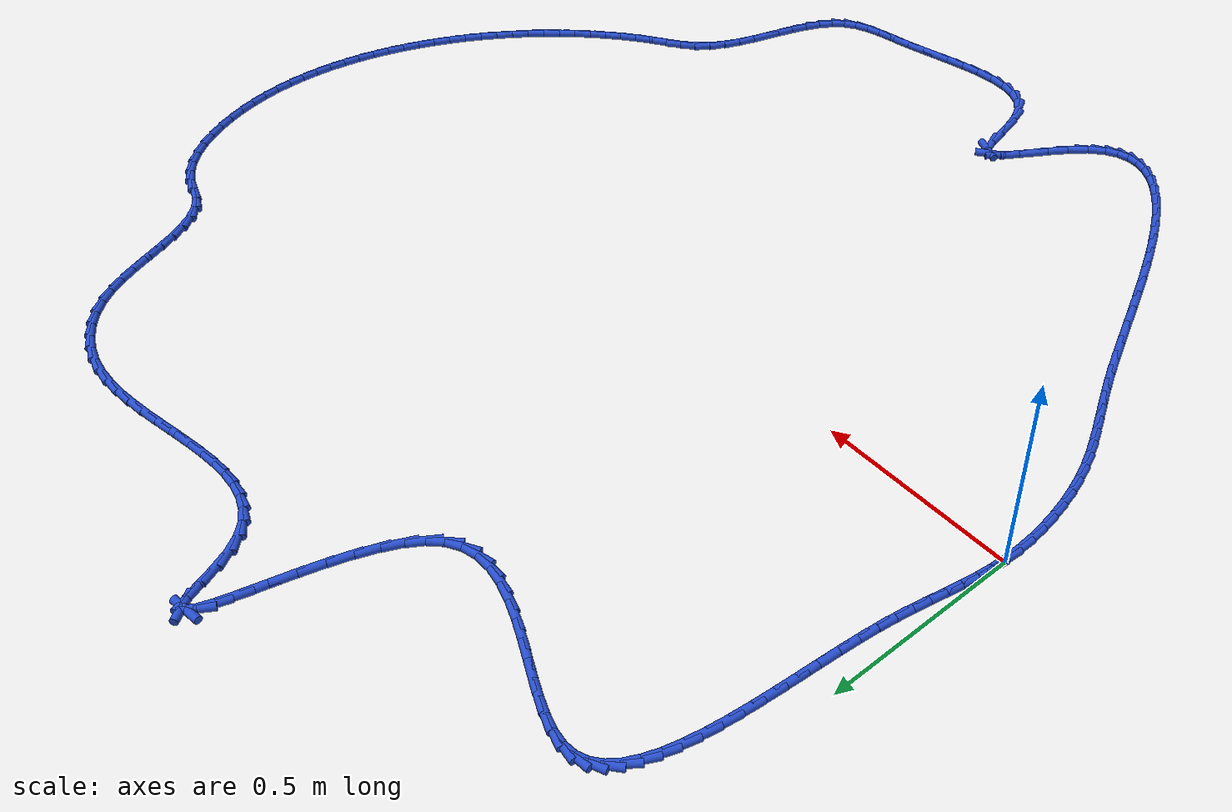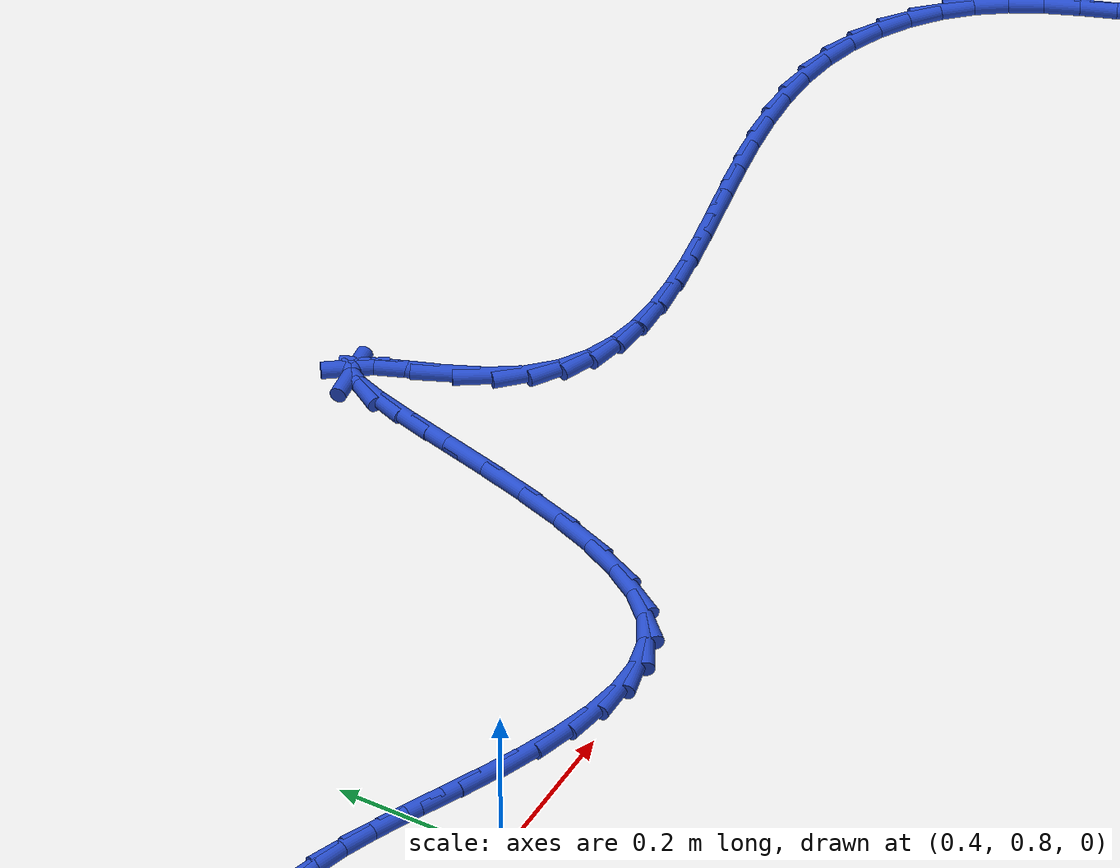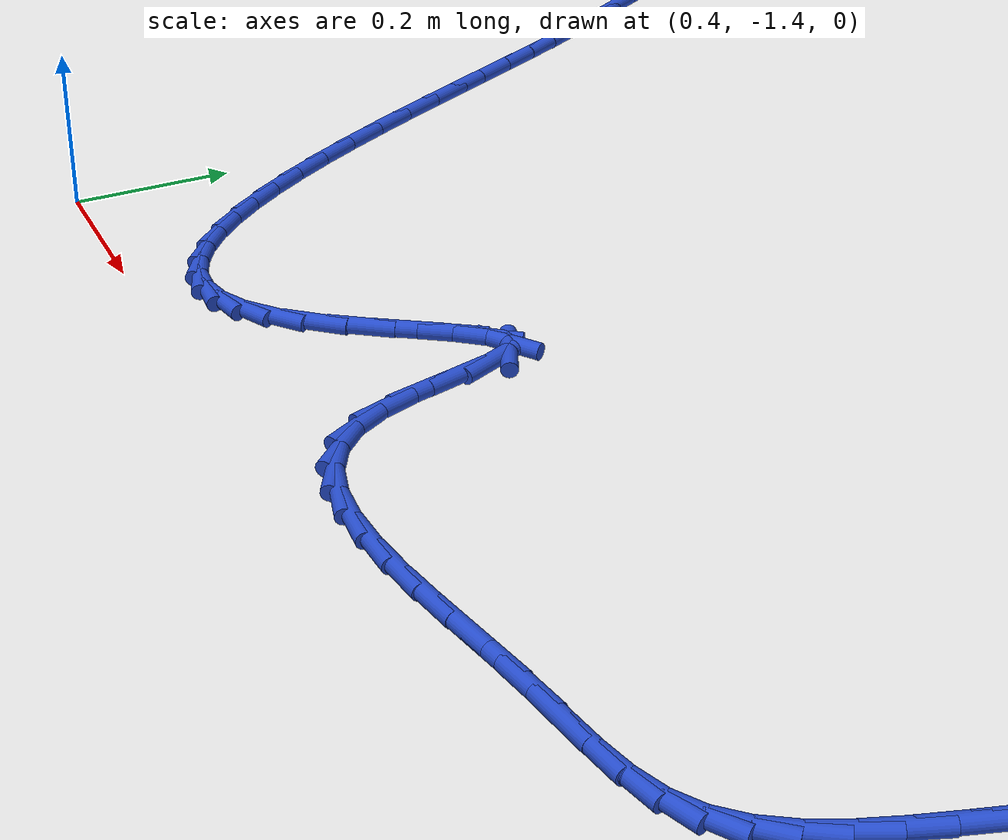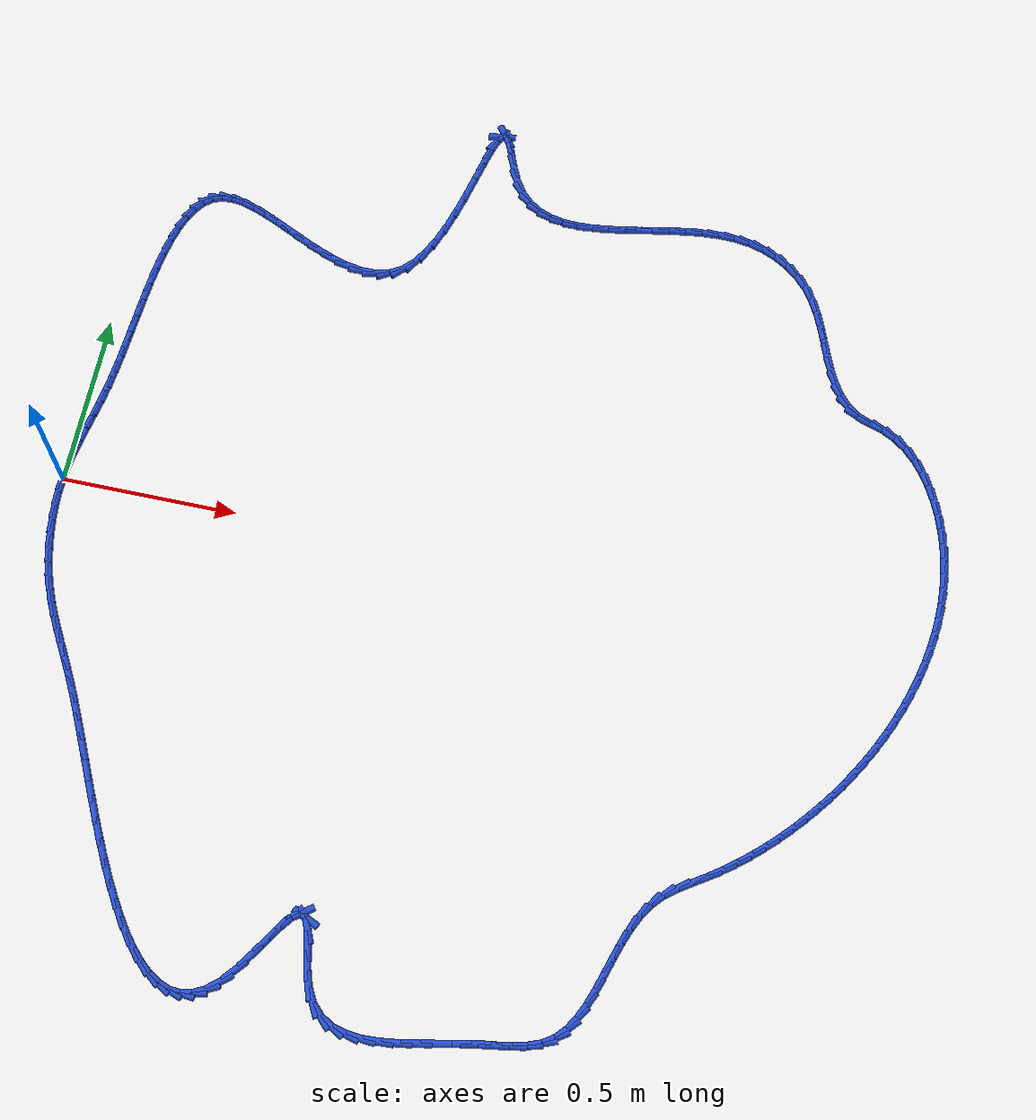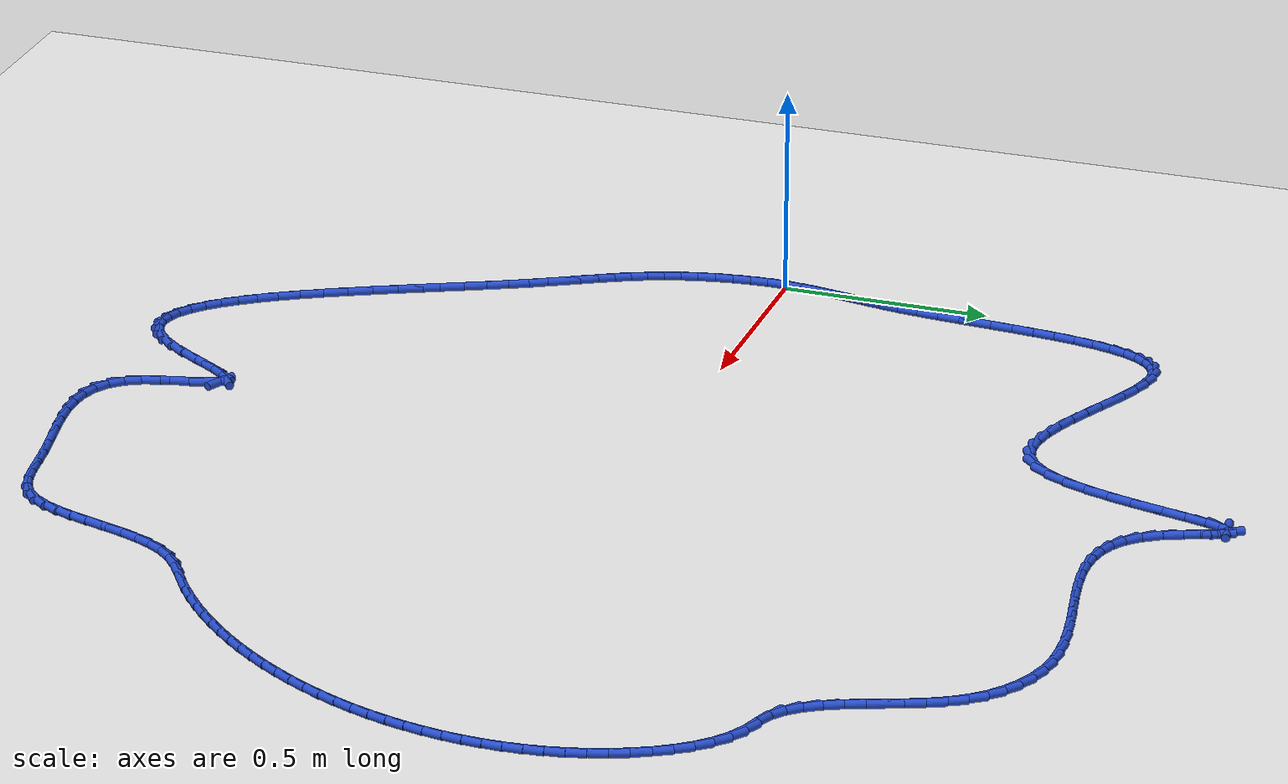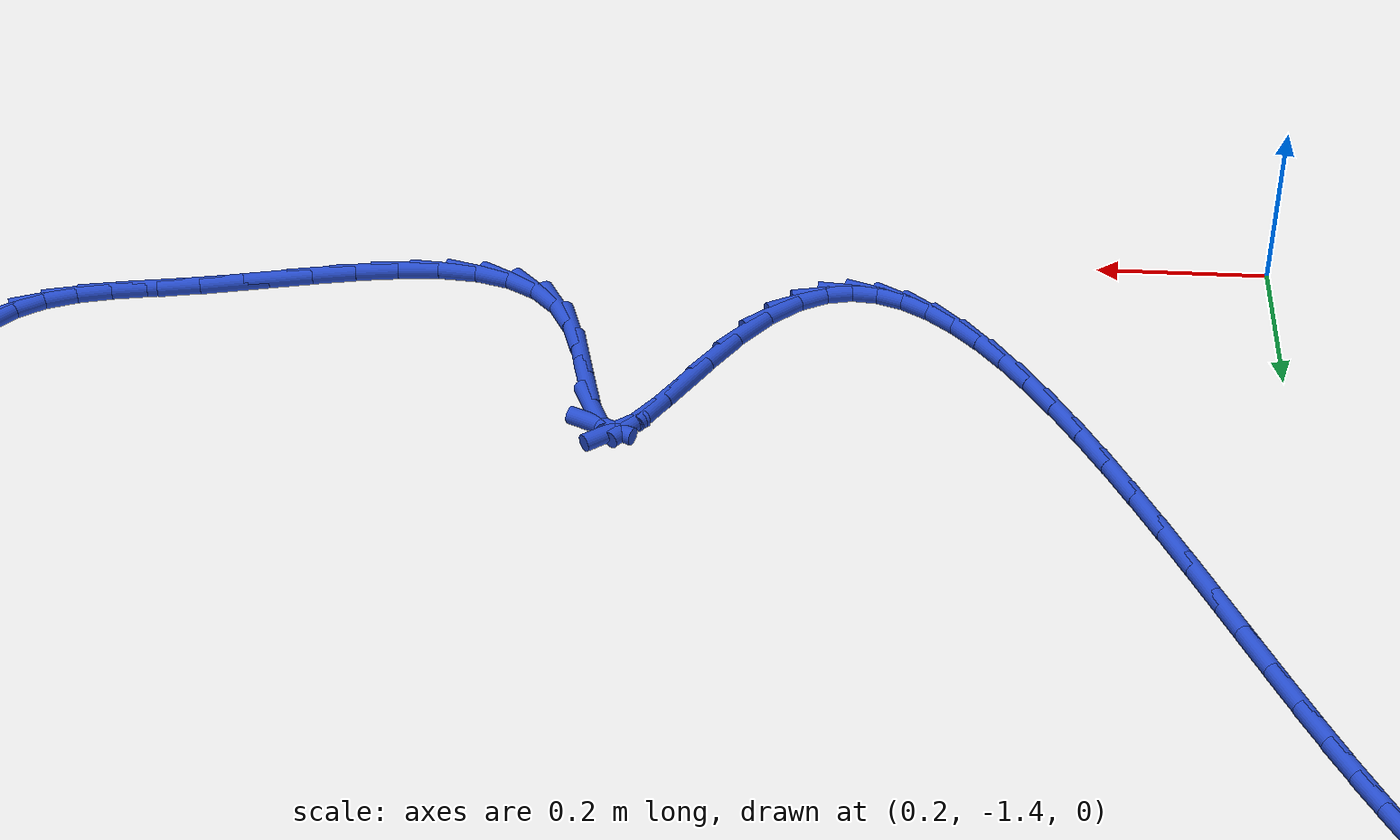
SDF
<sdf version="1.6">
 <world name="default">
  <light name="sun" type="directional">
   <pose>0 0 10 0 -0 0</pose>
   <diffuse>0.8 0.8 0.8 1</diffuse>
   <specular>0.2 0.2 0.2 1</specular>
   <attenuation>
    <range>1000</range>
    <constant>0.9</constant>
    <linear>0.01</linear>
    <quadratic>0.001</quadratic>
   </attenuation>
   <direction>-0.5 0.1 -0.9</direction>
  </light>
  <model name="ground_plane">
   <static>1</static>
   <link name="link">
    <collision name="collision">
     <geometry><plane><normal>0 0 1</normal><size>100 100</size></plane></geometry>
     <surface><friction><ode><mu>100</mu><mu2>50</mu2></ode></friction></surface>
    </collision>
    <visual name="visual">
     <cast_shadows>0</cast_shadows>
     <geometry><plane><normal>0 0 1</normal><size>100 100</size></plane></geometry>
     <material>
      <script><uri>file://media/materials/scripts/gazebo.material</uri><name>Gazebo/WhiteGlow</name></script>
     </material>
    </visual>
   </link>
  </model>
  <gravity>0 0 -9.8</gravity>
  <magnetic_field>6e-06 2.3e-05 -4.2e-05</magnetic_field>
  <atmosphere type="adiabatic"/>
  <physics name="default_physics" default="0" type="ode">
   <max_step_size>0.001</max_step_size>
   <real_time_factor>1</real_time_factor>
   <real_time_update_rate>1000</real_time_update_rate>
  </physics>
  <scene><ambient>0.4 0.4 0.4 1</ambient><background>0.7 0.7 0.7 1</background><shadows>1</shadows></scene>
  <spherical_coordinates>
   <surface_model>EARTH_WGS84</surface_model>
   <latitude_deg>0</latitude_deg>
   <longitude_deg>0</longitude_deg>
   <elevation>0</elevation>
   <heading_deg>0</heading_deg>
  </spherical_coordinates>
  <model name="line">
   <link name="link_0">
    <pose>-3.469446951953614e-17 -1.3877787807814457e-17 0.01 0 1.57 1.4951217058976023</pose>
    <collision name="collision">
     <geometry><cylinder><radius>0.01</radius><length>0.08</length></cylinder></geometry>
    </collision>
    <visual name="visual">
     <material>
      <script><name>Gazebo/Blue</name><uri>file://media/materials/scripts/gazebo.material</uri></script>
     </material>
     <geometry><cylinder><radius>0.01</radius><length>0.08</length></cylinder></geometry>
    </visual>
   </link>
   <link name="link_1">
    <pose>0.003068000607721073 0.04046458219282482 0.01 0 1.57 1.4431502194532113</pose>
    <collision name="collision">
     <geometry><cylinder><radius>0.01</radius><length>0.08</length></cylinder></geometry>
    </collision>
    <visual name="visual">
     <material>
      <script><name>Gazebo/Blue</name><uri>file://media/materials/scripts/gazebo.material</uri></script>
     </material>
     <geometry><cylinder><radius>0.01</radius><length>0.08</length></cylinder></geometry>
    </visual>
   </link>
   <link name="link_2">
    <pose>0.008171197587003923 0.080226472073507 0.01 0 1.57 1.4053528337721921</pose>
    <collision name="collision">
     <geometry><cylinder><radius>0.01</radius><length>0.08</length></cylinder></geometry>
    </collision>
    <visual name="visual">
     <material>
      <script><name>Gazebo/Blue</name><uri>file://media/materials/scripts/gazebo.material</uri></script>
     </material>
     <geometry><cylinder><radius>0.01</radius><length>0.08</length></cylinder></geometry>
    </visual>
   </link>
   <link name="link_3">
    <pose>0.014789591132992141 0.1198647662148879 0.01 0 1.57 1.383136226669687</pose>
    <collision name="collision">
     <geometry><cylinder><radius>0.01</radius><length>0.08</length></cylinder></geometry>
    </collision>
    <visual name="visual">
     <material>
      <script><name>Gazebo/Blue</name><uri>file://media/materials/scripts/gazebo.material</uri></script>
     </material>
     <geometry><cylinder><radius>0.01</radius><length>0.08</length></cylinder></geometry>
    </visual>
   </link>
   <link name="link_4">
    <pose>0.022403181440829364 0.15995856118980886 0.01 0 1.57 1.3766031780159855</pose>
    <collision name="collision">
     <geometry><cylinder><radius>0.01</radius><length>0.08</length></cylinder></geometry>
    </collision>
    <visual name="visual">
     <material>
      <script><name>Gazebo/Blue</name><uri>file://media/materials/scripts/gazebo.material</uri></script>
     </material>
     <geometry><cylinder><radius>0.01</radius><length>0.08</length></cylinder></geometry>
    </visual>
   </link>
   <link name="link_5">
    <pose>0.030491968705659216 0.20108695357111123 0.01 0 1.57 1.384773958833869</pose>
    <collision name="collision">
     <geometry><cylinder><radius>0.01</radius><length>0.08</length></cylinder></geometry>
    </collision>
    <visual name="visual">
     <material>
      <script><name>Gazebo/Blue</name><uri>file://media/materials/scripts/gazebo.material</uri></script>
     </material>
     <geometry><cylinder><radius>0.01</radius><length>0.08</length></cylinder></geometry>
    </visual>
   </link>
   <link name="link_6">
    <pose>0.038535953122625345 0.24382903993163638 0.01 0 1.57 1.4058634156009262</pose>
    <collision name="collision">
     <geometry><cylinder><radius>0.01</radius><length>0.08</length></cylinder></geometry>
    </collision>
    <visual name="visual">
     <material>
      <script><name>Gazebo/Blue</name><uri>file://media/materials/scripts/gazebo.material</uri></script>
     </material>
     <geometry><cylinder><radius>0.01</radius><length>0.08</length></cylinder></geometry>
    </visual>
   </link>
   <link name="link_7">
    <pose>0.04601513488687137 0.2887639168442257 0.01 0 1.57 1.4368984109076222</pose>
    <collision name="collision">
     <geometry><cylinder><radius>0.01</radius><length>0.08</length></cylinder></geometry>
    </collision>
    <visual name="visual">
     <material>
      <script><name>Gazebo/Blue</name><uri>file://media/materials/scripts/gazebo.material</uri></script>
     </material>
     <geometry><cylinder><radius>0.01</radius><length>0.08</length></cylinder></geometry>
    </visual>
   </link>
   <link name="link_8">
    <pose>0.05243608313809826 0.33643104656350636 0.01 0 1.57 1.4652924382436097</pose>
    <collision name="collision">
     <geometry><cylinder><radius>0.01</radius><length>0.08</length></cylinder></geometry>
    </collision>
    <visual name="visual">
     <material>
      <script><name>Gazebo/Blue</name><uri>file://media/materials/scripts/gazebo.material</uri></script>
     </material>
     <geometry><cylinder><radius>0.01</radius><length>0.08</length></cylinder></geometry>
    </visual>
   </link>
   <link name="link_9">
    <pose>0.05775873869656523 0.386693572515644 0.01 0 1.57 1.4835040604561711</pose>
    <collision name="collision">
     <geometry><cylinder><radius>0.01</radius><length>0.08</length></cylinder></geometry>
    </collision>
    <visual name="visual">
     <material>
      <script><name>Gazebo/Blue</name><uri>file://media/materials/scripts/gazebo.material</uri></script>
     </material>
     <geometry><cylinder><radius>0.01</radius><length>0.08</length></cylinder></geometry>
    </visual>
   </link>
   <link name="link_10">
    <pose>0.06232300132376176 0.4388478330152007 0.01 0 1.57 1.4929879269007387</pose>
    <collision name="collision">
     <geometry><cylinder><radius>0.01</radius><length>0.08</length></cylinder></geometry>
    </collision>
    <visual name="visual">
     <material>
      <script><name>Gazebo/Blue</name><uri>file://media/materials/scripts/gazebo.material</uri></script>
     </material>
     <geometry><cylinder><radius>0.01</radius><length>0.08</length></cylinder></geometry>
    </visual>
   </link>
   <link name="link_11">
    <pose>0.06648051340331826 0.49217264927809773 0.01 0 1.57 1.494654360328666</pose>
    <collision name="collision">
     <geometry><cylinder><radius>0.01</radius><length>0.08</length></cylinder></geometry>
    </collision>
    <visual name="visual">
     <material>
      <script><name>Gazebo/Blue</name><uri>file://media/materials/scripts/gazebo.material</uri></script>
     </material>
     <geometry><cylinder><radius>0.01</radius><length>0.08</length></cylinder></geometry>
    </visual>
   </link>
   <link name="link_12">
    <pose>0.07058291731886508 0.545946842520256 0.01 0 1.57 1.4887613804122766</pose>
    <collision name="collision">
     <geometry><cylinder><radius>0.01</radius><length>0.08</length></cylinder></geometry>
    </collision>
    <visual name="visual">
     <material>
      <script><name>Gazebo/Blue</name><uri>file://media/materials/scripts/gazebo.material</uri></script>
     </material>
     <geometry><cylinder><radius>0.01</radius><length>0.08</length></cylinder></geometry>
    </visual>
   </link>
   <link name="link_13">
    <pose>0.0749818554540327 0.5994492339575973 0.01 0 1.57 1.4749724110111586</pose>
    <collision name="collision">
     <geometry><cylinder><radius>0.01</radius><length>0.08</length></cylinder></geometry>
    </collision>
    <visual name="visual">
     <material>
      <script><name>Gazebo/Blue</name><uri>file://media/materials/scripts/gazebo.material</uri></script>
     </material>
     <geometry><cylinder><radius>0.01</radius><length>0.08</length></cylinder></geometry>
    </visual>
   </link>
   <link name="link_14">
    <pose>0.08002897019245148 0.6519586448060424 0.01 0 1.57 1.4523086974725221</pose>
    <collision name="collision">
     <geometry><cylinder><radius>0.01</radius><length>0.08</length></cylinder></geometry>
    </collision>
    <visual name="visual">
     <material>
      <script><name>Gazebo/Blue</name><uri>file://media/materials/scripts/gazebo.material</uri></script>
     </material>
     <geometry><cylinder><radius>0.01</radius><length>0.08</length></cylinder></geometry>
    </visual>
   </link>
   <link name="link_15">
    <pose>0.08607590391775174 0.7027538962815124 0.01 0 1.57 1.4189872636883354</pose>
    <collision name="collision">
     <geometry><cylinder><radius>0.01</radius><length>0.08</length></cylinder></geometry>
    </collision>
    <visual name="visual">
     <material>
      <script><name>Gazebo/Blue</name><uri>file://media/materials/scripts/gazebo.material</uri></script>
     </material>
     <geometry><cylinder><radius>0.01</radius><length>0.08</length></cylinder></geometry>
    </visual>
   </link>
   <link name="link_16">
    <pose>0.09347429901356401 0.7511138095999289 0.01 0 1.57 1.3721073862547013</pose>
    <collision name="collision">
     <geometry><cylinder><radius>0.01</radius><length>0.08</length></cylinder></geometry>
    </collision>
    <visual name="visual">
     <material>
      <script><name>Gazebo/Blue</name><uri>file://media/materials/scripts/gazebo.material</uri></script>
     </material>
     <geometry><cylinder><radius>0.01</radius><length>0.08</length></cylinder></geometry>
    </visual>
   </link>
   <link name="link_17">
    <pose>0.10257579786351859 0.7963172059772129 0.01 0 1.57 1.3071227031823986</pose>
    <collision name="collision">
     <geometry><cylinder><radius>0.01</radius><length>0.08</length></cylinder></geometry>
    </collision>
    <visual name="visual">
     <material>
      <script><name>Gazebo/Blue</name><uri>file://media/materials/scripts/gazebo.material</uri></script>
     </material>
     <geometry><cylinder><radius>0.01</radius><length>0.08</length></cylinder></geometry>
    </visual>
   </link>
   <link name="link_18">
    <pose>0.1137320428512459 0.8376429066292856 0.01 0 1.57 1.2170462354324274</pose>
    <collision name="collision">
     <geometry><cylinder><radius>0.01</radius><length>0.08</length></cylinder></geometry>
    </collision>
    <visual name="visual">
     <material>
      <script><name>Gazebo/Blue</name><uri>file://media/materials/scripts/gazebo.material</uri></script>
     </material>
     <geometry><cylinder><radius>0.01</radius><length>0.08</length></cylinder></geometry>
    </visual>
   </link>
   <link name="link_19">
    <pose>0.12729467636037634 0.874369732772068 0.01 0 1.57 1.0915491959882178</pose>
    <collision name="collision">
     <geometry><cylinder><radius>0.01</radius><length>0.08</length></cylinder></geometry>
    </collision>
    <visual name="visual">
     <material>
      <script><name>Gazebo/Blue</name><uri>file://media/materials/scripts/gazebo.material</uri></script>
     </material>
     <geometry><cylinder><radius>0.01</radius><length>0.08</length></cylinder></geometry>
    </visual>
   </link>
   <link name="link_20">
    <pose>0.14361534077454038 0.9057765056214819 0.01 0 1.57 0.917125326420871</pose>
    <collision name="collision">
     <geometry><cylinder><radius>0.01</radius><length>0.08</length></cylinder></geometry>
    </collision>
    <visual name="visual">
     <material>
      <script><name>Gazebo/Blue</name><uri>file://media/materials/scripts/gazebo.material</uri></script>
     </material>
     <geometry><cylinder><radius>0.01</radius><length>0.08</length></cylinder></geometry>
    </visual>
   </link>
   <link name="link_21">
    <pose>0.16304567847736823 0.9311420463934474 0.01 0 1.57 0.6824128942961104</pose>
    <collision name="collision">
     <geometry><cylinder><radius>0.01</radius><length>0.08</length></cylinder></geometry>
    </collision>
    <visual name="visual">
     <material>
      <script><name>Gazebo/Blue</name><uri>file://media/materials/scripts/gazebo.material</uri></script>
     </material>
     <geometry><cylinder><radius>0.01</radius><length>0.08</length></cylinder></geometry>
    </visual>
   </link>
   <link name="link_22">
    <pose>0.1859373318524905 0.9497451763038873 0.01 0 1.57 0.39455558384039596</pose>
    <collision name="collision">
     <geometry><cylinder><radius>0.01</radius><length>0.08</length></cylinder></geometry>
    </collision>
    <visual name="visual">
     <material>
      <script><name>Gazebo/Blue</name><uri>file://media/materials/scripts/gazebo.material</uri></script>
     </material>
     <geometry><cylinder><radius>0.01</radius><length>0.08</length></cylinder></geometry>
    </visual>
   </link>
   <link name="link_23">
    <pose>0.2126419432835375 0.9608647165687213 0.01 0 1.57 0.09520336615453237</pose>
    <collision name="collision">
     <geometry><cylinder><radius>0.01</radius><length>0.08</length></cylinder></geometry>
    </collision>
    <visual name="visual">
     <material>
      <script><name>Gazebo/Blue</name><uri>file://media/materials/scripts/gazebo.material</uri></script>
     </material>
     <geometry><cylinder><radius>0.01</radius><length>0.08</length></cylinder></geometry>
    </visual>
   </link>
   <link name="link_24">
    <pose>0.24349739040757096 0.9638111662760462 0.01 0 1.57 -0.14008450777462744</pose>
    <collision name="collision">
     <geometry><cylinder><radius>0.01</radius><length>0.08</length></cylinder></geometry>
    </collision>
    <visual name="visual">
     <material>
      <script><name>Gazebo/Blue</name><uri>file://media/materials/scripts/gazebo.material</uri></script>
     </material>
     <geometry><cylinder><radius>0.01</radius><length>0.08</length></cylinder></geometry>
    </visual>
   </link>
   <link name="link_25">
    <pose>0.27840999056388943 0.9588882074890405 0.01 0 1.57 -0.2869290451556819</pose>
    <collision name="collision">
     <geometry><cylinder><radius>0.01</radius><length>0.08</length></cylinder></geometry>
    </collision>
    <visual name="visual">
     <material>
      <script><name>Gazebo/Blue</name><uri>file://media/materials/scripts/gazebo.material</uri></script>
     </material>
     <geometry><cylinder><radius>0.01</radius><length>0.08</length></cylinder></geometry>
    </visual>
   </link>
   <link name="link_26">
    <pose>0.3167789259476304 0.9475666314647947 0.01 0 1.57 -0.37430686810902347</pose>
    <collision name="collision">
     <geometry><cylinder><radius>0.01</radius><length>0.08</length></cylinder></geometry>
    </collision>
    <visual name="visual">
     <material>
      <script><name>Gazebo/Blue</name><uri>file://media/materials/scripts/gazebo.material</uri></script>
     </material>
     <geometry><cylinder><radius>0.01</radius><length>0.08</length></cylinder></geometry>
    </visual>
   </link>
   <link name="link_27">
    <pose>0.35797437554632305 0.9313839767774466 0.01 0 1.57 -0.4224653980475397</pose>
    <collision name="collision">
     <geometry><cylinder><radius>0.01</radius><length>0.08</length></cylinder></geometry>
    </collision>
    <visual name="visual">
     <material>
      <script><name>Gazebo/Blue</name><uri>file://media/materials/scripts/gazebo.material</uri></script>
     </material>
     <geometry><cylinder><radius>0.01</radius><length>0.08</length></cylinder></geometry>
    </visual>
   </link>
   <link name="link_28">
    <pose>0.4013665183474964 0.9118777820011319 0.01 0 1.57 -0.4422982987916948</pose>
    <collision name="collision">
     <geometry><cylinder><radius>0.01</radius><length>0.08</length></cylinder></geometry>
    </collision>
    <visual name="visual">
     <material>
      <script><name>Gazebo/Blue</name><uri>file://media/materials/scripts/gazebo.material</uri></script>
     </material>
     <geometry><cylinder><radius>0.01</radius><length>0.08</length></cylinder></geometry>
    </visual>
   </link>
   <link name="link_29">
    <pose>0.4463255333386797 0.8905855857099881 0.01 0 1.57 -0.43881658580921684</pose>
    <collision name="collision">
     <geometry><cylinder><radius>0.01</radius><length>0.08</length></cylinder></geometry>
    </collision>
    <visual name="visual">
     <material>
      <script><name>Gazebo/Blue</name><uri>file://media/materials/scripts/gazebo.material</uri></script>
     </material>
     <geometry><cylinder><radius>0.01</radius><length>0.08</length></cylinder></geometry>
    </visual>
   </link>
   <link name="link_30">
    <pose>0.4922215995074023 0.8690449264781515 0.01 0 1.57 -0.4130940439720531</pose>
    <collision name="collision">
     <geometry><cylinder><radius>0.01</radius><length>0.08</length></cylinder></geometry>
    </collision>
    <visual name="visual">
     <material>
      <script><name>Gazebo/Blue</name><uri>file://media/materials/scripts/gazebo.material</uri></script>
     </material>
     <geometry><cylinder><radius>0.01</radius><length>0.08</length></cylinder></geometry>
    </visual>
   </link>
   <link name="link_31">
    <pose>0.5384248958411935 0.8487933428797588 0.01 0 1.57 -0.3629622806388114</pose>
    <collision name="collision">
     <geometry><cylinder><radius>0.01</radius><length>0.08</length></cylinder></geometry>
    </collision>
    <visual name="visual">
     <material>
      <script><name>Gazebo/Blue</name><uri>file://media/materials/scripts/gazebo.material</uri></script>
     </material>
     <geometry><cylinder><radius>0.01</radius><length>0.08</length></cylinder></geometry>
    </visual>
   </link>
   <link name="link_32">
    <pose>0.5843056013275824 0.8313683734889473 0.01 0 1.57 -0.28290631552987117</pose>
    <collision name="collision">
     <geometry><cylinder><radius>0.01</radius><length>0.08</length></cylinder></geometry>
    </collision>
    <visual name="visual">
     <material>
      <script><name>Gazebo/Blue</name><uri>file://media/materials/scripts/gazebo.material</uri></script>
     </material>
     <geometry><cylinder><radius>0.01</radius><length>0.08</length></cylinder></geometry>
    </visual>
   </link>
   <link name="link_33">
    <pose>0.6292338949540979 0.8183075568798531 0.01 0 1.57 -0.16368439228024606</pose>
    <collision name="collision">
     <geometry><cylinder><radius>0.01</radius><length>0.08</length></cylinder></geometry>
    </collision>
    <visual name="visual">
     <material>
      <script><name>Gazebo/Blue</name><uri>file://media/materials/scripts/gazebo.material</uri></script>
     </material>
     <geometry><cylinder><radius>0.01</radius><length>0.08</length></cylinder></geometry>
    </visual>
   </link>
   <link name="link_34">
    <pose>0.6725799557082695 0.8111484316266135 0.01 0 1.57 0.006809459342512383</pose>
    <collision name="collision">
     <geometry><cylinder><radius>0.01</radius><length>0.08</length></cylinder></geometry>
    </collision>
    <visual name="visual">
     <material>
      <script><name>Gazebo/Blue</name><uri>file://media/materials/scripts/gazebo.material</uri></script>
     </material>
     <geometry><cylinder><radius>0.01</radius><length>0.08</length></cylinder></geometry>
    </visual>
   </link>
   <link name="link_35">
    <pose>0.7137139625776263 0.8114285363033651 0.01 0 1.57 0.23719285076958105</pose>
    <collision name="collision">
     <geometry><cylinder><radius>0.01</radius><length>0.08</length></cylinder></geometry>
    </collision>
    <visual name="visual">
     <material>
      <script><name>Gazebo/Blue</name><uri>file://media/materials/scripts/gazebo.material</uri></script>
     </material>
     <geometry><cylinder><radius>0.01</radius><length>0.08</length></cylinder></geometry>
    </visual>
   </link>
   <link name="link_36">
    <pose>0.7520060945496978 0.8206854094842446 0.01 0 1.57 0.516409422108368</pose>
    <collision name="collision">
     <geometry><cylinder><radius>0.01</radius><length>0.08</length></cylinder></geometry>
    </collision>
    <visual name="visual">
     <material>
      <script><name>Gazebo/Blue</name><uri>file://media/materials/scripts/gazebo.material</uri></script>
     </material>
     <geometry><cylinder><radius>0.01</radius><length>0.08</length></cylinder></geometry>
    </visual>
   </link>
   <link name="link_37">
    <pose>0.7868265306120127 0.8404565897433887 0.01 0 1.57 0.7985524834558605</pose>
    <collision name="collision">
     <geometry><cylinder><radius>0.01</radius><length>0.08</length></cylinder></geometry>
    </collision>
    <visual name="visual">
     <material>
      <script><name>Gazebo/Blue</name><uri>file://media/materials/scripts/gazebo.material</uri></script>
     </material>
     <geometry><cylinder><radius>0.01</radius><length>0.08</length></cylinder></geometry>
    </visual>
   </link>
   <link name="link_38">
    <pose>0.8176031347495035 0.8720537253443836 0.01 0 1.57 1.0059609943322232</pose>
    <collision name="collision">
     <geometry><cylinder><radius>0.01</radius><length>0.08</length></cylinder></geometry>
    </collision>
    <visual name="visual">
     <material>
      <script><name>Gazebo/Blue</name><uri>file://media/materials/scripts/gazebo.material</uri></script>
     </material>
     <geometry><cylinder><radius>0.01</radius><length>0.08</length></cylinder></geometry>
    </visual>
   </link>
   <link name="link_39">
    <pose>0.8443922377049559 0.9143274338236977 0.01 0 1.57 1.1378254809079609</pose>
    <collision name="collision">
     <geometry><cylinder><radius>0.01</radius><length>0.08</length></cylinder></geometry>
    </collision>
    <visual name="visual">
     <material>
      <script><name>Gazebo/Blue</name><uri>file://media/materials/scripts/gazebo.material</uri></script>
     </material>
     <geometry><cylinder><radius>0.01</radius><length>0.08</length></cylinder></geometry>
    </visual>
   </link>
   <link name="link_40">
    <pose>0.8676364884619845 0.9646155382075973 0.01 0 1.57 1.2232509794631061</pose>
    <collision name="collision">
     <geometry><cylinder><radius>0.01</radius><length>0.08</length></cylinder></geometry>
    </collision>
    <visual name="visual">
     <material>
      <script><name>Gazebo/Blue</name><uri>file://media/materials/scripts/gazebo.material</uri></script>
     </material>
     <geometry><cylinder><radius>0.01</radius><length>0.08</length></cylinder></geometry>
    </visual>
   </link>
   <link name="link_41">
    <pose>0.8877841667137211 1.0202338120679193 0.01 0 1.57 1.279022746159319</pose>
    <collision name="collision">
     <geometry><cylinder><radius>0.01</radius><length>0.08</length></cylinder></geometry>
    </collision>
    <visual name="visual">
     <material>
      <script><name>Gazebo/Blue</name><uri>file://media/materials/scripts/gazebo.material</uri></script>
     </material>
     <geometry><cylinder><radius>0.01</radius><length>0.08</length></cylinder></geometry>
    </visual>
   </link>
   <link name="link_42">
    <pose>0.9052835521532973 1.0784980289764992 0.01 0 1.57 1.3138459610086088</pose>
    <collision name="collision">
     <geometry><cylinder><radius>0.01</radius><length>0.08</length></cylinder></geometry>
    </collision>
    <visual name="visual">
     <material>
      <script><name>Gazebo/Blue</name><uri>file://media/materials/scripts/gazebo.material</uri></script>
     </material>
     <geometry><cylinder><radius>0.01</radius><length>0.08</length></cylinder></geometry>
    </visual>
   </link>
   <link name="link_43">
    <pose>0.9205829244738453 1.1367239625051744 0.01 0 1.57 1.3313909660755805</pose>
    <collision name="collision">
     <geometry><cylinder><radius>0.01</radius><length>0.08</length></cylinder></geometry>
    </collision>
    <visual name="visual">
     <material>
      <script><name>Gazebo/Blue</name><uri>file://media/materials/scripts/gazebo.material</uri></script>
     </material>
     <geometry><cylinder><radius>0.01</radius><length>0.08</length></cylinder></geometry>
    </visual>
   </link>
   <link name="link_44">
    <pose>0.9341305633684974 1.1922273862257815 0.01 0 1.57 1.3310847076183943</pose>
    <collision name="collision">
     <geometry><cylinder><radius>0.01</radius><length>0.08</length></cylinder></geometry>
    </collision>
    <visual name="visual">
     <material>
      <script><name>Gazebo/Blue</name><uri>file://media/materials/scripts/gazebo.material</uri></script>
     </material>
     <geometry><cylinder><radius>0.01</radius><length>0.08</length></cylinder></geometry>
    </visual>
   </link>
   <link name="link_45">
    <pose>0.9463747485303853 1.2423240737101562 0.01 0 1.57 1.3060315951407147</pose>
    <collision name="collision">
     <geometry><cylinder><radius>0.01</radius><length>0.08</length></cylinder></geometry>
    </collision>
    <visual name="visual">
     <material>
      <script><name>Gazebo/Blue</name><uri>file://media/materials/scripts/gazebo.material</uri></script>
     </material>
     <geometry><cylinder><radius>0.01</radius><length>0.08</length></cylinder></geometry>
    </visual>
   </link>
   <link name="link_46">
    <pose>0.9577637596526409 1.2843297985301356 0.01 0 1.57 1.2326552124681993</pose>
    <collision name="collision">
     <geometry><cylinder><radius>0.01</radius><length>0.08</length></cylinder></geometry>
    </collision>
    <visual name="visual">
     <material>
      <script><name>Gazebo/Blue</name><uri>file://media/materials/scripts/gazebo.material</uri></script>
     </material>
     <geometry><cylinder><radius>0.01</radius><length>0.08</length></cylinder></geometry>
    </visual>
   </link>
   <link name="link_47">
    <pose>0.9687458764283959 1.3155603342575553 0.01 0 1.57 1.0155808294025885</pose>
    <collision name="collision">
     <geometry><cylinder><radius>0.01</radius><length>0.08</length></cylinder></geometry>
    </collision>
    <visual name="visual">
     <material>
      <script><name>Gazebo/Blue</name><uri>file://media/materials/scripts/gazebo.material</uri></script>
     </material>
     <geometry><cylinder><radius>0.01</radius><length>0.08</length></cylinder></geometry>
    </visual>
   </link>
   <link name="link_48">
    <pose>0.979769378550783 1.3333314544642525 0.01 0 1.57 0.14042758504457697</pose>
    <collision name="collision">
     <geometry><cylinder><radius>0.01</radius><length>0.08</length></cylinder></geometry>
    </collision>
    <visual name="visual">
     <material>
      <script><name>Gazebo/Blue</name><uri>file://media/materials/scripts/gazebo.material</uri></script>
     </material>
     <geometry><cylinder><radius>0.01</radius><length>0.08</length></cylinder></geometry>
    </visual>
   </link>
   <link name="link_49">
    <pose>0.9912825457129333 1.334958932722063 0.01 0 1.57 -0.9414782304646425</pose>
    <collision name="collision">
     <geometry><cylinder><radius>0.01</radius><length>0.08</length></cylinder></geometry>
    </collision>
    <visual name="visual">
     <material>
      <script><name>Gazebo/Blue</name><uri>file://media/materials/scripts/gazebo.material</uri></script>
     </material>
     <geometry><cylinder><radius>0.01</radius><length>0.08</length></cylinder></geometry>
    </visual>
   </link>
   <link name="link_50">
    <pose>1.0037374971588184 1.3178521475267506 0.01 0 1.57 -1.1802746688257668</pose>
    <collision name="collision">
     <geometry><cylinder><radius>0.01</radius><length>0.08</length></cylinder></geometry>
    </collision>
    <visual name="visual">
     <material>
      <script><name>Gazebo/Blue</name><uri>file://media/materials/scripts/gazebo.material</uri></script>
     </material>
     <geometry><cylinder><radius>0.01</radius><length>0.08</length></cylinder></geometry>
    </visual>
   </link>
   <link name="link_51">
    <pose>1.0177650497429502 1.283776970344599 0.01 0 1.57 -1.2060451095904092</pose>
    <collision name="collision">
     <geometry><cylinder><radius>0.01</radius><length>0.08</length></cylinder></geometry>
    </collision>
    <visual name="visual">
     <material>
      <script><name>Gazebo/Blue</name><uri>file://media/materials/scripts/gazebo.material</uri></script>
     </material>
     <geometry><cylinder><radius>0.01</radius><length>0.08</length></cylinder></geometry>
    </visual>
   </link>
   <link name="link_52">
    <pose>1.034246783044417 1.2406126506751738 0.01 0 1.57 -1.1465453344732879</pose>
    <collision name="collision">
     <geometry><cylinder><radius>0.01</radius><length>0.08</length></cylinder></geometry>
    </collision>
    <visual name="visual">
     <material>
      <script><name>Gazebo/Blue</name><uri>file://media/materials/scripts/gazebo.material</uri></script>
     </material>
     <geometry><cylinder><radius>0.01</radius><length>0.08</length></cylinder></geometry>
    </visual>
   </link>
   <link name="link_53">
    <pose>1.0540830498803222 1.1966961133009113 0.01 0 1.57 -0.9964386643646291</pose>
    <collision name="collision">
     <geometry><cylinder><radius>0.01</radius><length>0.08</length></cylinder></geometry>
    </collision>
    <visual name="visual">
     <material>
      <script><name>Gazebo/Blue</name><uri>file://media/materials/scripts/gazebo.material</uri></script>
     </material>
     <geometry><cylinder><radius>0.01</radius><length>0.08</length></cylinder></geometry>
    </visual>
   </link>
   <link name="link_54">
    <pose>1.0780716258764036 1.1596271535343536 0.01 0 1.57 -0.7899394217756761</pose>
    <collision name="collision">
     <geometry><cylinder><radius>0.01</radius><length>0.08</length></cylinder></geometry>
    </collision>
    <visual name="visual">
     <material>
      <script><name>Gazebo/Blue</name><uri>file://media/materials/scripts/gazebo.material</uri></script>
     </material>
     <geometry><cylinder><radius>0.01</radius><length>0.08</length></cylinder></geometry>
    </visual>
   </link>
   <link name="link_55">
    <pose>1.1062072440000357 1.1312348256375389 0.01 0 1.57 -0.5735198520284591</pose>
    <collision name="collision">
     <geometry><cylinder><radius>0.01</radius><length>0.08</length></cylinder></geometry>
    </collision>
    <visual name="visual">
     <material>
      <script><name>Gazebo/Blue</name><uri>file://media/materials/scripts/gazebo.material</uri></script>
     </material>
     <geometry><cylinder><radius>0.01</radius><length>0.08</length></cylinder></geometry>
    </visual>
   </link>
   <link name="link_56">
    <pose>1.13810634460546 1.1106297371138358 0.01 0 1.57 -0.37099968447056125</pose>
    <collision name="collision">
     <geometry><cylinder><radius>0.01</radius><length>0.08</length></cylinder></geometry>
    </collision>
    <visual name="visual">
     <material>
      <script><name>Gazebo/Blue</name><uri>file://media/materials/scripts/gazebo.material</uri></script>
     </material>
     <geometry><cylinder><radius>0.01</radius><length>0.08</length></cylinder></geometry>
    </visual>
   </link>
   <link name="link_57">
    <pose>1.1733831527396918 1.096906576057819 0.01 0 1.57 -0.19972609045565312</pose>
    <collision name="collision">
     <geometry><cylinder><radius>0.01</radius><length>0.08</length></cylinder></geometry>
    </collision>
    <visual name="visual">
     <material>
      <script><name>Gazebo/Blue</name><uri>file://media/materials/scripts/gazebo.material</uri></script>
     </material>
     <geometry><cylinder><radius>0.01</radius><length>0.08</length></cylinder></geometry>
    </visual>
   </link>
   <link name="link_58">
    <pose>1.211651893449744 1.0891600305640612 0.01 0 1.57 -0.06535628984153605</pose>
    <collision name="collision">
     <geometry><cylinder><radius>0.01</radius><length>0.08</length></cylinder></geometry>
    </collision>
    <visual name="visual">
     <material>
      <script><name>Gazebo/Blue</name><uri>file://media/materials/scripts/gazebo.material</uri></script>
     </material>
     <geometry><cylinder><radius>0.01</radius><length>0.08</length></cylinder></geometry>
    </visual>
   </link>
   <link name="link_59">
    <pose>1.2525267917826328 1.0864847887271372 0.01 0 1.57 0.0345781648088882</pose>
    <collision name="collision">
     <geometry><cylinder><radius>0.01</radius><length>0.08</length></cylinder></geometry>
    </collision>
    <visual name="visual">
     <material>
      <script><name>Gazebo/Blue</name><uri>file://media/materials/scripts/gazebo.material</uri></script>
     </material>
     <geometry><cylinder><radius>0.01</radius><length>0.08</length></cylinder></geometry>
    </visual>
   </link>
   <link name="link_60">
    <pose>1.2956220727853711 1.08797553864162 0.01 0 1.57 0.10536049077298286</pose>
    <collision name="collision">
     <geometry><cylinder><radius>0.01</radius><length>0.08</length></cylinder></geometry>
    </collision>
    <visual name="visual">
     <material>
      <script><name>Gazebo/Blue</name><uri>file://media/materials/scripts/gazebo.material</uri></script>
     </material>
     <geometry><cylinder><radius>0.01</radius><length>0.08</length></cylinder></geometry>
    </visual>
   </link>
   <link name="link_61">
    <pose>1.3405519615049741 1.0927269684020842 0.01 0 1.57 0.15205128804951173</pose>
    <collision name="collision">
     <geometry><cylinder><radius>0.01</radius><length>0.08</length></cylinder></geometry>
    </collision>
    <visual name="visual">
     <material>
      <script><name>Gazebo/Blue</name><uri>file://media/materials/scripts/gazebo.material</uri></script>
     </material>
     <geometry><cylinder><radius>0.01</radius><length>0.08</length></cylinder></geometry>
    </visual>
   </link>
   <link name="link_62">
    <pose>1.3869306829884562 1.099833766103103 0.01 0 1.57 0.1784468122634462</pose>
    <collision name="collision">
     <geometry><cylinder><radius>0.01</radius><length>0.08</length></cylinder></geometry>
    </collision>
    <visual name="visual">
     <material>
      <script><name>Gazebo/Blue</name><uri>file://media/materials/scripts/gazebo.material</uri></script>
     </material>
     <geometry><cylinder><radius>0.01</radius><length>0.08</length></cylinder></geometry>
    </visual>
   </link>
   <link name="link_63">
    <pose>1.4343724622828316 1.1083906198392504 0.01 0 1.57 0.18693897201468798</pose>
    <collision name="collision">
     <geometry><cylinder><radius>0.01</radius><length>0.08</length></cylinder></geometry>
    </collision>
    <visual name="visual">
     <material>
      <script><name>Gazebo/Blue</name><uri>file://media/materials/scripts/gazebo.material</uri></script>
     </material>
     <geometry><cylinder><radius>0.01</radius><length>0.08</length></cylinder></geometry>
    </visual>
   </link>
   <link name="link_64">
    <pose>1.4824915244351147 1.1174922177051008 0.01 0 1.57 0.17863566192941252</pose>
    <collision name="collision">
     <geometry><cylinder><radius>0.01</radius><length>0.08</length></cylinder></geometry>
    </collision>
    <visual name="visual">
     <material>
      <script><name>Gazebo/Blue</name><uri>file://media/materials/scripts/gazebo.material</uri></script>
     </material>
     <geometry><cylinder><radius>0.01</radius><length>0.08</length></cylinder></geometry>
    </visual>
   </link>
   <link name="link_65">
    <pose>1.5309020944923195 1.126233247795227 0.01 0 1.57 0.1534958237025379</pose>
    <collision name="collision">
     <geometry><cylinder><radius>0.01</radius><length>0.08</length></cylinder></geometry>
    </collision>
    <visual name="visual">
     <material>
      <script><name>Gazebo/Blue</name><uri>file://media/materials/scripts/gazebo.material</uri></script>
     </material>
     <geometry><cylinder><radius>0.01</radius><length>0.08</length></cylinder></geometry>
    </visual>
   </link>
   <link name="link_66">
    <pose>1.5792183975014606 1.1337083982042033 0.01 0 1.57 0.11042632487577428</pose>
    <collision name="collision">
     <geometry><cylinder><radius>0.01</radius><length>0.08</length></cylinder></geometry>
    </collision>
    <visual name="visual">
     <material>
      <script><name>Gazebo/Blue</name><uri>file://media/materials/scripts/gazebo.material</uri></script>
     </material>
     <geometry><cylinder><radius>0.01</radius><length>0.08</length></cylinder></geometry>
    </visual>
   </link>
   <link name="link_67">
    <pose>1.6270546585095529 1.1390123570266035 0.01 0 1.57 0.0473869867652983</pose>
    <collision name="collision">
     <geometry><cylinder><radius>0.01</radius><length>0.08</length></cylinder></geometry>
    </collision>
    <visual name="visual">
     <material>
      <script><name>Gazebo/Blue</name><uri>file://media/materials/scripts/gazebo.material</uri></script>
     </material>
     <geometry><cylinder><radius>0.01</radius><length>0.08</length></cylinder></geometry>
    </visual>
   </link>
   <link name="link_68">
    <pose>1.6740251025636104 1.1412398123570016 0.01 0 1.57 -0.038353975724134015</pose>
    <collision name="collision">
     <geometry><cylinder><radius>0.01</radius><length>0.08</length></cylinder></geometry>
    </collision>
    <visual name="visual">
     <material>
      <script><name>Gazebo/Blue</name><uri>file://media/materials/scripts/gazebo.material</uri></script>
     </material>
     <geometry><cylinder><radius>0.01</radius><length>0.08</length></cylinder></geometry>
    </visual>
   </link>
   <link name="link_69">
    <pose>1.719743954710647 1.1394854522899707 0.01 0 1.57 -0.14941839314027158</pose>
    <collision name="collision">
     <geometry><cylinder><radius>0.01</radius><length>0.08</length></cylinder></geometry>
    </collision>
    <visual name="visual">
     <material>
      <script><name>Gazebo/Blue</name><uri>file://media/materials/scripts/gazebo.material</uri></script>
     </material>
     <geometry><cylinder><radius>0.01</radius><length>0.08</length></cylinder></geometry>
    </visual>
   </link>
   <link name="link_70">
    <pose>1.7638250343301367 1.1328494698820264 0.01 0 1.57 -0.2786030383575921</pose>
    <collision name="collision">
     <geometry><cylinder><radius>0.01</radius><length>0.08</length></cylinder></geometry>
    </collision>
    <visual name="visual">
     <material>
      <script><name>Gazebo/Blue</name><uri>file://media/materials/scripts/gazebo.material</uri></script>
     </material>
     <geometry><cylinder><radius>0.01</radius><length>0.08</length></cylinder></geometry>
    </visual>
   </link>
   <link name="link_71">
    <pose>1.8058530065400327 1.1208276853565793 0.01 0 1.57 -0.411804718498776</pose>
    <collision name="collision">
     <geometry><cylinder><radius>0.01</radius><length>0.08</length></cylinder></geometry>
    </collision>
    <visual name="visual">
     <material>
      <script><name>Gazebo/Blue</name><uri>file://media/materials/scripts/gazebo.material</uri></script>
     </material>
     <geometry><cylinder><radius>0.01</radius><length>0.08</length></cylinder></geometry>
    </visual>
   </link>
   <link name="link_72">
    <pose>1.8453643375607671 1.1035699843216642 0.01 0 1.57 -0.547763148569805</pose>
    <collision name="collision">
     <geometry><cylinder><radius>0.01</radius><length>0.08</length></cylinder></geometry>
    </collision>
    <visual name="visual">
     <material>
      <script><name>Gazebo/Blue</name><uri>file://media/materials/scripts/gazebo.material</uri></script>
     </material>
     <geometry><cylinder><radius>0.01</radius><length>0.08</length></cylinder></geometry>
    </visual>
   </link>
   <link name="link_73">
    <pose>1.8818909745806631 1.0812875762459606 0.01 0 1.57 -0.6863712183992837</pose>
    <collision name="collision">
     <geometry><cylinder><radius>0.01</radius><length>0.08</length></cylinder></geometry>
    </collision>
    <visual name="visual">
     <material>
      <script><name>Gazebo/Blue</name><uri>file://media/materials/scripts/gazebo.material</uri></script>
     </material>
     <geometry><cylinder><radius>0.01</radius><length>0.08</length></cylinder></geometry>
    </visual>
   </link>
   <link name="link_74">
    <pose>1.9149648647880422 1.0541916705981473 0.01 0 1.57 -0.827198770863257</pose>
    <collision name="collision">
     <geometry><cylinder><radius>0.01</radius><length>0.08</length></cylinder></geometry>
    </collision>
    <visual name="visual">
     <material>
      <script><name>Gazebo/Blue</name><uri>file://media/materials/scripts/gazebo.material</uri></script>
     </material>
     <geometry><cylinder><radius>0.01</radius><length>0.08</length></cylinder></geometry>
    </visual>
   </link>
   <link name="link_75">
    <pose>1.9441179553712273 1.0224934768469034 0.01 0 1.57 -0.9681049488302428</pose>
    <collision name="collision">
     <geometry><cylinder><radius>0.01</radius><length>0.08</length></cylinder></geometry>
    </collision>
    <visual name="visual">
     <material>
      <script><name>Gazebo/Blue</name><uri>file://media/materials/scripts/gazebo.material</uri></script>
     </material>
     <geometry><cylinder><radius>0.01</radius><length>0.08</length></cylinder></geometry>
    </visual>
   </link>
   <link name="link_76">
    <pose>1.9689297718805145 0.9864347777618683 0.01 0 1.57 -1.0857923786347483</pose>
    <collision name="collision">
     <geometry><cylinder><radius>0.01</radius><length>0.08</length></cylinder></geometry>
    </collision>
    <visual name="visual">
     <material>
      <script><name>Gazebo/Blue</name><uri>file://media/materials/scripts/gazebo.material</uri></script>
     </material>
     <geometry><cylinder><radius>0.01</radius><length>0.08</length></cylinder></geometry>
    </visual>
   </link>
   <link name="link_77">
    <pose>1.9898187080595495 0.9467964030381781 0.01 0 1.57 -1.163647870618194</pose>
    <collision name="collision">
     <geometry><cylinder><radius>0.01</radius><length>0.08</length></cylinder></geometry>
    </collision>
    <visual name="visual">
     <material>
      <script><name>Gazebo/Blue</name><uri>file://media/materials/scripts/gazebo.material</uri></script>
     </material>
     <geometry><cylinder><radius>0.01</radius><length>0.08</length></cylinder></geometry>
    </visual>
   </link>
   <link name="link_78">
    <pose>2.0079207113468343 0.9048202740134405 0.01 0 1.57 -1.2053691886753586</pose>
    <collision name="collision">
     <geometry><cylinder><radius>0.01</radius><length>0.08</length></cylinder></geometry>
    </collision>
    <visual name="visual">
     <material>
      <script><name>Gazebo/Blue</name><uri>file://media/materials/scripts/gazebo.material</uri></script>
     </material>
     <geometry><cylinder><radius>0.01</radius><length>0.08</length></cylinder></geometry>
    </visual>
   </link>
   <link name="link_79">
    <pose>2.024394858906696 0.8617631749175427 0.01 0 1.57 -1.2135622303266547</pose>
    <collision name="collision">
     <geometry><cylinder><radius>0.01</radius><length>0.08</length></cylinder></geometry>
    </collision>
    <visual name="visual">
     <material>
      <script><name>Gazebo/Blue</name><uri>file://media/materials/scripts/gazebo.material</uri></script>
     </material>
     <geometry><cylinder><radius>0.01</radius><length>0.08</length></cylinder></geometry>
    </visual>
   </link>
   <link name="link_80">
    <pose>2.0404002279034636 0.8188818899803719 0.01 0 1.57 -1.1878756528247416</pose>
    <collision name="collision">
     <geometry><cylinder><radius>0.01</radius><length>0.08</length></cylinder></geometry>
    </collision>
    <visual name="visual">
     <material>
      <script><name>Gazebo/Blue</name><uri>file://media/materials/scripts/gazebo.material</uri></script>
     </material>
     <geometry><cylinder><radius>0.01</radius><length>0.08</length></cylinder></geometry>
    </visual>
   </link>
   <link name="link_81">
    <pose>2.0570958955014644 0.7774332034318159 0.01 0 1.57 -1.1245231275320537</pose>
    <collision name="collision">
     <geometry><cylinder><radius>0.01</radius><length>0.08</length></cylinder></geometry>
    </collision>
    <visual name="visual">
     <material>
      <script><name>Gazebo/Blue</name><uri>file://media/materials/scripts/gazebo.material</uri></script>
     </material>
     <geometry><cylinder><radius>0.01</radius><length>0.08</length></cylinder></geometry>
    </visual>
   </link>
   <link name="link_82">
    <pose>2.075640938865028 0.7386738995017615 0.01 0 1.57 -1.0164367772035008</pose>
    <collision name="collision">
     <geometry><cylinder><radius>0.01</radius><length>0.08</length></cylinder></geometry>
    </collision>
    <visual name="visual">
     <material>
      <script><name>Gazebo/Blue</name><uri>file://media/materials/scripts/gazebo.material</uri></script>
     </material>
     <geometry><cylinder><radius>0.01</radius><length>0.08</length></cylinder></geometry>
    </visual>
   </link>
   <link name="link_83">
    <pose>2.0971944351584804 0.7038607624200963 0.01 0 1.57 -0.8555714627965555</pose>
    <collision name="collision">
     <geometry><cylinder><radius>0.01</radius><length>0.08</length></cylinder></geometry>
    </collision>
    <visual name="visual">
     <material>
      <script><name>Gazebo/Blue</name><uri>file://media/materials/scripts/gazebo.material</uri></script>
     </material>
     <geometry><cylinder><radius>0.01</radius><length>0.08</length></cylinder></geometry>
    </visual>
   </link>
   <link name="link_84">
    <pose>2.12291546154615 0.6742505764167075 0.01 0 1.57 -0.6407067921363031</pose>
    <collision name="collision">
     <geometry><cylinder><radius>0.01</radius><length>0.08</length></cylinder></geometry>
    </collision>
    <visual name="visual">
     <material>
      <script><name>Gazebo/Blue</name><uri>file://media/materials/scripts/gazebo.material</uri></script>
     </material>
     <geometry><cylinder><radius>0.01</radius><length>0.08</length></cylinder></geometry>
    </visual>
   </link>
   <link name="link_85">
    <pose>2.1539630951923665 0.6511001257214823 0.01 0 1.57 -0.39601721792617645</pose>
    <collision name="collision">
     <geometry><cylinder><radius>0.01</radius><length>0.08</length></cylinder></geometry>
    </collision>
    <visual name="visual">
     <material>
      <script><name>Gazebo/Blue</name><uri>file://media/materials/scripts/gazebo.material</uri></script>
     </material>
     <geometry><cylinder><radius>0.01</radius><length>0.08</length></cylinder></geometry>
    </visual>
   </link>
   <link name="link_86">
    <pose>2.1913532682345194 0.635467056369339 0.01 0 1.57 -0.3189362826762241</pose>
    <collision name="collision">
     <geometry><cylinder><radius>0.01</radius><length>0.08</length></cylinder></geometry>
    </collision>
    <visual name="visual">
     <material>
      <script><name>Gazebo/Blue</name><uri>file://media/materials/scripts/gazebo.material</uri></script>
     </material>
     <geometry><cylinder><radius>0.01</radius><length>0.08</length></cylinder></geometry>
    </visual>
   </link>
   <link name="link_87">
    <pose>2.231616586133669 0.6221717348677379 0.01 0 1.57 -0.4770995167074334</pose>
    <collision name="collision">
     <geometry><cylinder><radius>0.01</radius><length>0.08</length></cylinder></geometry>
    </collision>
    <visual name="visual">
     <material>
      <script><name>Gazebo/Blue</name><uri>file://media/materials/scripts/gazebo.material</uri></script>
     </material>
     <geometry><cylinder><radius>0.01</radius><length>0.08</length></cylinder></geometry>
    </visual>
   </link>
   <link name="link_88">
    <pose>2.268812657128706 0.6029439782686185 0.01 0 1.57 -0.6448412242707166</pose>
    <collision name="collision">
     <geometry><cylinder><radius>0.01</radius><length>0.08</length></cylinder></geometry>
    </collision>
    <visual name="visual">
     <material>
      <script><name>Gazebo/Blue</name><uri>file://media/materials/scripts/gazebo.material</uri></script>
     </material>
     <geometry><cylinder><radius>0.01</radius><length>0.08</length></cylinder></geometry>
    </visual>
   </link>
   <link name="link_89">
    <pose>2.3023825707190997 0.5776961792482437 0.01 0 1.57 -0.7897595406359486</pose>
    <collision name="collision">
     <geometry><cylinder><radius>0.01</radius><length>0.08</length></cylinder></geometry>
    </collision>
    <visual name="visual">
     <material>
      <script><name>Gazebo/Blue</name><uri>file://media/materials/scripts/gazebo.material</uri></script>
     </material>
     <geometry><cylinder><radius>0.01</radius><length>0.08</length></cylinder></geometry>
    </visual>
   </link>
   <link name="link_90">
    <pose>2.3324466110636592 0.5473687472407215 0.01 0 1.57 -0.9120884586671185</pose>
    <collision name="collision">
     <geometry><cylinder><radius>0.01</radius><length>0.08</length></cylinder></geometry>
    </collision>
    <visual name="visual">
     <material>
      <script><name>Gazebo/Blue</name><uri>file://media/materials/scripts/gazebo.material</uri></script>
     </material>
     <geometry><cylinder><radius>0.01</radius><length>0.08</length></cylinder></geometry>
    </visual>
   </link>
   <link name="link_91">
    <pose>2.3591250623211986 0.5129020916801605 0.01 0 1.57 -1.0146401314525444</pose>
    <collision name="collision">
     <geometry><cylinder><radius>0.01</radius><length>0.08</length></cylinder></geometry>
    </collision>
    <visual name="visual">
     <material>
      <script><name>Gazebo/Blue</name><uri>file://media/materials/scripts/gazebo.material</uri></script>
     </material>
     <geometry><cylinder><radius>0.01</radius><length>0.08</length></cylinder></geometry>
    </visual>
   </link>
   <link name="link_92">
    <pose>2.382538208650529 0.47523662200066935 0.01 0 1.57 -1.1010321141788486</pose>
    <collision name="collision">
     <geometry><cylinder><radius>0.01</radius><length>0.08</length></cylinder></geometry>
    </collision>
    <visual name="visual">
     <material>
      <script><name>Gazebo/Blue</name><uri>file://media/materials/scripts/gazebo.material</uri></script>
     </material>
     <geometry><cylinder><radius>0.01</radius><length>0.08</length></cylinder></geometry>
    </visual>
   </link>
   <link name="link_93">
    <pose>2.4028063342104624 0.43531274763635613 0.01 0 1.57 -1.1748579690619192</pose>
    <collision name="collision">
     <geometry><cylinder><radius>0.01</radius><length>0.08</length></cylinder></geometry>
    </collision>
    <visual name="visual">
     <material>
      <script><name>Gazebo/Blue</name><uri>file://media/materials/scripts/gazebo.material</uri></script>
     </material>
     <geometry><cylinder><radius>0.01</radius><length>0.08</length></cylinder></geometry>
    </visual>
   </link>
   <link name="link_94">
    <pose>2.4200493303554063 0.3940629148728059 0.01 0 1.57 -1.2420887907445428</pose>
    <collision name="collision">
     <geometry><cylinder><radius>0.01</radius><length>0.08</length></cylinder></geometry>
    </collision>
    <visual name="visual">
     <material>
      <script><name>Gazebo/Blue</name><uri>file://media/materials/scripts/gazebo.material</uri></script>
     </material>
     <geometry><cylinder><radius>0.01</radius><length>0.08</length></cylinder></geometry>
    </visual>
   </link>
   <link name="link_95">
    <pose>2.434370159267804 0.35207637244097806 0.01 0 1.57 -1.3075979759672174</pose>
    <collision name="collision">
     <geometry><cylinder><radius>0.01</radius><length>0.08</length></cylinder></geometry>
    </collision>
    <visual name="visual">
     <material>
      <script><name>Gazebo/Blue</name><uri>file://media/materials/scripts/gazebo.material</uri></script>
     </material>
     <geometry><cylinder><radius>0.01</radius><length>0.08</length></cylinder></geometry>
    </visual>
   </link>
   <link name="link_96">
    <pose>2.445848780602093 0.3094760490781601 0.01 0 1.57 -1.3713986083399323</pose>
    <collision name="collision">
     <geometry><cylinder><radius>0.01</radius><length>0.08</length></cylinder></geometry>
    </collision>
    <visual name="visual">
     <material>
      <script><name>Gazebo/Blue</name><uri>file://media/materials/scripts/gazebo.material</uri></script>
     </material>
     <geometry><cylinder><radius>0.01</radius><length>0.08</length></cylinder></geometry>
    </visual>
   </link>
   <link name="link_97">
    <pose>2.454563510638193 0.26635155812284605 0.01 0 1.57 -1.4332568355106787</pose>
    <collision name="collision">
     <geometry><cylinder><radius>0.01</radius><length>0.08</length></cylinder></geometry>
    </collision>
    <visual name="visual">
     <material>
      <script><name>Gazebo/Blue</name><uri>file://media/materials/scripts/gazebo.material</uri></script>
     </material>
     <geometry><cylinder><radius>0.01</radius><length>0.08</length></cylinder></geometry>
    </visual>
   </link>
   <link name="link_98">
    <pose>2.4605926656560215 0.2227925129135312 0.01 0 1.57 -1.4930131295486242</pose>
    <collision name="collision">
     <geometry><cylinder><radius>0.01</radius><length>0.08</length></cylinder></geometry>
    </collision>
    <visual name="visual">
     <material>
      <script><name>Gazebo/Blue</name><uri>file://media/materials/scripts/gazebo.material</uri></script>
     </material>
     <geometry><cylinder><radius>0.01</radius><length>0.08</length></cylinder></geometry>
    </visual>
   </link>
   <link name="link_99">
    <pose>2.4640145619354996 0.1788885267887105 0.01 0 1.57 -1.5505778934114505</pose>
    <collision name="collision">
     <geometry><cylinder><radius>0.01</radius><length>0.08</length></cylinder></geometry>
    </collision>
    <visual name="visual">
     <material>
      <script><name>Gazebo/Blue</name><uri>file://media/materials/scripts/gazebo.material</uri></script>
     </material>
     <geometry><cylinder><radius>0.01</radius><length>0.08</length></cylinder></geometry>
    </visual>
   </link>
   <link name="link_100">
    <pose>2.464907515756545 0.13472921308687905 0.01 0 1.57 1.5356687322598306</pose>
    <collision name="collision">
     <geometry><cylinder><radius>0.01</radius><length>0.08</length></cylinder></geometry>
    </collision>
    <visual name="visual">
     <material>
      <script><name>Gazebo/Blue</name><uri>file://media/materials/scripts/gazebo.material</uri></script>
     </material>
     <geometry><cylinder><radius>0.01</radius><length>0.08</length></cylinder></geometry>
    </visual>
   </link>
   <link name="link_101">
    <pose>2.463349843399079 0.09040418514653177 0.01 0 1.57 1.482515519305764</pose>
    <collision name="collision">
     <geometry><cylinder><radius>0.01</radius><length>0.08</length></cylinder></geometry>
    </collision>
    <visual name="visual">
     <material>
      <script><name>Gazebo/Blue</name><uri>file://media/materials/scripts/gazebo.material</uri></script>
     </material>
     <geometry><cylinder><radius>0.01</radius><length>0.08</length></cylinder></geometry>
    </visual>
   </link>
   <link name="link_102">
    <pose>2.4594198611430205 0.04600305630616357 0.01 0 1.57 1.4314858515382165</pose>
    <collision name="collision">
     <geometry><cylinder><radius>0.01</radius><length>0.08</length></cylinder></geometry>
    </collision>
    <visual name="visual">
     <material>
      <script><name>Gazebo/Blue</name><uri>file://media/materials/scripts/gazebo.material</uri></script>
     </material>
     <geometry><cylinder><radius>0.01</radius><length>0.08</length></cylinder></geometry>
    </visual>
   </link>
   <link name="link_103">
    <pose>2.4531958852682885 0.001615439904269253 0.01 0 1.57 1.3824765006985245</pose>
    <collision name="collision">
     <geometry><cylinder><radius>0.01</radius><length>0.08</length></cylinder></geometry>
    </collision>
    <visual name="visual">
     <material>
      <script><name>Gazebo/Blue</name><uri>file://media/materials/scripts/gazebo.material</uri></script>
     </material>
     <geometry><cylinder><radius>0.01</radius><length>0.08</length></cylinder></geometry>
    </visual>
   </link>
   <link name="link_104">
    <pose>2.444756232054803 -0.042669050720656035 0.01 0 1.57 1.3353587032412921</pose>
    <collision name="collision">
     <geometry><cylinder><radius>0.01</radius><length>0.08</length></cylinder></geometry>
    </collision>
    <visual name="visual">
     <material>
      <script><name>Gazebo/Blue</name><uri>file://media/materials/scripts/gazebo.material</uri></script>
     </material>
     <geometry><cylinder><radius>0.01</radius><length>0.08</length></cylinder></geometry>
    </visual>
   </link>
   <link name="link_105">
    <pose>2.4341792177824826 -0.0867608022301174 0.01 0 1.57 1.2899853141110689</pose>
    <collision name="collision">
     <geometry><cylinder><radius>0.01</radius><length>0.08</length></cylinder></geometry>
    </collision>
    <visual name="visual">
     <material>
      <script><name>Gazebo/Blue</name><uri>file://media/materials/scripts/gazebo.material</uri></script>
     </material>
     <geometry><cylinder><radius>0.01</radius><length>0.08</length></cylinder></geometry>
    </visual>
   </link>
   <link name="link_106">
    <pose>2.421543158731248 -0.13057020128561989 0.01 0 1.57 1.2461965978270022</pose>
    <collision name="collision">
     <geometry><cylinder><radius>0.01</radius><length>0.08</length></cylinder></geometry>
    </collision>
    <visual name="visual">
     <material>
      <script><name>Gazebo/Blue</name><uri>file://media/materials/scripts/gazebo.material</uri></script>
     </material>
     <geometry><cylinder><radius>0.01</radius><length>0.08</length></cylinder></geometry>
    </visual>
   </link>
   <link name="link_107">
    <pose>2.406926371181018 -0.17400763454866863 0.01 0 1.57 1.2038247029825826</pose>
    <collision name="collision">
     <geometry><cylinder><radius>0.01</radius><length>0.08</length></cylinder></geometry>
    </collision>
    <visual name="visual">
     <material>
      <script><name>Gazebo/Blue</name><uri>file://media/materials/scripts/gazebo.material</uri></script>
     </material>
     <geometry><cylinder><radius>0.01</radius><length>0.08</length></cylinder></geometry>
    </visual>
   </link>
   <link name="link_108">
    <pose>2.390407171411711 -0.21698348868076855 0.01 0 1.57 1.1626969467034307</pose>
    <collision name="collision">
     <geometry><cylinder><radius>0.01</radius><length>0.08</length></cylinder></geometry>
    </collision>
    <visual name="visual">
     <material>
      <script><name>Gazebo/Blue</name><uri>file://media/materials/scripts/gazebo.material</uri></script>
     </material>
     <geometry><cylinder><radius>0.01</radius><length>0.08</length></cylinder></geometry>
    </visual>
   </link>
   <link name="link_109">
    <pose>2.3720638757032475 -0.25940815034342474 0.01 0 1.57 1.122638072122885</pose>
    <collision name="collision">
     <geometry><cylinder><radius>0.01</radius><length>0.08</length></cylinder></geometry>
    </collision>
    <visual name="visual">
     <material>
      <script><name>Gazebo/Blue</name><uri>file://media/materials/scripts/gazebo.material</uri></script>
     </material>
     <geometry><cylinder><radius>0.01</radius><length>0.08</length></cylinder></geometry>
    </visual>
   </link>
   <link name="link_110">
    <pose>2.3519748003355483 -0.30119200619814224 0.01 0 1.57 1.0834716491369403</pose>
    <collision name="collision">
     <geometry><cylinder><radius>0.01</radius><length>0.08</length></cylinder></geometry>
    </collision>
    <visual name="visual">
     <material>
      <script><name>Gazebo/Blue</name><uri>file://media/materials/scripts/gazebo.material</uri></script>
     </material>
     <geometry><cylinder><radius>0.01</radius><length>0.08</length></cylinder></geometry>
    </visual>
   </link>
   <link name="link_111">
    <pose>2.3302182615885303 -0.3422454429064261 0.01 0 1.57 1.0450207785749936</pose>
    <collision name="collision">
     <geometry><cylinder><radius>0.01</radius><length>0.08</length></cylinder></geometry>
    </collision>
    <visual name="visual">
     <material>
      <script><name>Gazebo/Blue</name><uri>file://media/materials/scripts/gazebo.material</uri></script>
     </material>
     <geometry><cylinder><radius>0.01</radius><length>0.08</length></cylinder></geometry>
    </visual>
   </link>
   <link name="link_112">
    <pose>2.3068725757421142 -0.3824788471297815 0.01 0 1.57 1.0071082412878738</pose>
    <collision name="collision">
     <geometry><cylinder><radius>0.01</radius><length>0.08</length></cylinder></geometry>
    </collision>
    <visual name="visual">
     <material>
      <script><name>Gazebo/Blue</name><uri>file://media/materials/scripts/gazebo.material</uri></script>
     </material>
     <geometry><cylinder><radius>0.01</radius><length>0.08</length></cylinder></geometry>
    </visual>
   </link>
   <link name="link_113">
    <pose>2.28201605907622 -0.4218026055297134 0.01 0 1.57 0.9695562124955402</pose>
    <collision name="collision">
     <geometry><cylinder><radius>0.01</radius><length>0.08</length></cylinder></geometry>
    </collision>
    <visual name="visual">
     <material>
      <script><name>Gazebo/Blue</name><uri>file://media/materials/scripts/gazebo.material</uri></script>
     </material>
     <geometry><cylinder><radius>0.01</radius><length>0.08</length></cylinder></geometry>
    </visual>
   </link>
   <link name="link_114">
    <pose>2.2557270278707664 -0.4601271047677268 0.01 0 1.57 0.932185641843404</pose>
    <collision name="collision">
     <geometry><cylinder><radius>0.01</radius><length>0.08</length></cylinder></geometry>
    </collision>
    <visual name="visual">
     <material>
      <script><name>Gazebo/Blue</name><uri>file://media/materials/scripts/gazebo.material</uri></script>
     </material>
     <geometry><cylinder><radius>0.01</radius><length>0.08</length></cylinder></geometry>
    </visual>
   </link>
   <link name="link_115">
    <pose>2.228083798405672 -0.4973627315053266 0.01 0 1.57 0.8948153833047394</pose>
    <collision name="collision">
     <geometry><cylinder><radius>0.01</radius><length>0.08</length></cylinder></geometry>
    </collision>
    <visual name="visual">
     <material>
      <script><name>Gazebo/Blue</name><uri>file://media/materials/scripts/gazebo.material</uri></script>
     </material>
     <geometry><cylinder><radius>0.01</radius><length>0.08</length></cylinder></geometry>
    </visual>
   </link>
   <link name="link_116">
    <pose>2.199164686960859 -0.5334198724040174 0.01 0 1.57 0.8572611477602697</pose>
    <collision name="collision">
     <geometry><cylinder><radius>0.01</radius><length>0.08</length></cylinder></geometry>
    </collision>
    <visual name="visual">
     <material>
      <script><name>Gazebo/Blue</name><uri>file://media/materials/scripts/gazebo.material</uri></script>
     </material>
     <geometry><cylinder><radius>0.01</radius><length>0.08</length></cylinder></geometry>
    </visual>
   </link>
   <link name="link_117">
    <pose>2.169048009816244 -0.5682089141253057 0.01 0 1.57 0.8193343457972647</pose>
    <collision name="collision">
     <geometry><cylinder><radius>0.01</radius><length>0.08</length></cylinder></geometry>
    </collision>
    <visual name="visual">
     <material>
      <script><name>Gazebo/Blue</name><uri>file://media/materials/scripts/gazebo.material</uri></script>
     </material>
     <geometry><cylinder><radius>0.01</radius><length>0.08</length></cylinder></geometry>
    </visual>
   </link>
   <link name="link_118">
    <pose>2.137812083251748 -0.6016402433306958 0.01 0 1.57 0.7808408899324684</pose>
    <collision name="collision">
     <geometry><cylinder><radius>0.01</radius><length>0.08</length></cylinder></geometry>
    </collision>
    <visual name="visual">
     <material>
      <script><name>Gazebo/Blue</name><uri>file://media/materials/scripts/gazebo.material</uri></script>
     </material>
     <geometry><cylinder><radius>0.01</radius><length>0.08</length></cylinder></geometry>
    </visual>
   </link>
   <link name="link_119">
    <pose>2.1055352235472897 -0.6336242466816926 0.01 0 1.57 0.7415800351777757</pose>
    <collision name="collision">
     <geometry><cylinder><radius>0.01</radius><length>0.08</length></cylinder></geometry>
    </collision>
    <visual name="visual">
     <material>
      <script><name>Gazebo/Blue</name><uri>file://media/materials/scripts/gazebo.material</uri></script>
     </material>
     <geometry><cylinder><radius>0.01</radius><length>0.08</length></cylinder></geometry>
    </visual>
   </link>
   <link name="link_120">
    <pose>2.072295746982789 -0.6640713108398013 0.01 0 1.57 0.70134335601474</pose>
    <collision name="collision">
     <geometry><cylinder><radius>0.01</radius><length>0.08</length></cylinder></geometry>
    </collision>
    <visual name="visual">
     <material>
      <script><name>Gazebo/Blue</name><uri>file://media/materials/scripts/gazebo.material</uri></script>
     </material>
     <geometry><cylinder><radius>0.01</radius><length>0.08</length></cylinder></geometry>
    </visual>
   </link>
   <link name="link_121">
    <pose>2.0381719698381637 -0.6928918224665266 0.01 0 1.57 0.659913988112757</pose>
    <collision name="collision">
     <geometry><cylinder><radius>0.01</radius><length>0.08</length></cylinder></geometry>
    </collision>
    <visual name="visual">
     <material>
      <script><name>Gazebo/Blue</name><uri>file://media/materials/scripts/gazebo.material</uri></script>
     </material>
     <geometry><cylinder><radius>0.01</radius><length>0.08</length></cylinder></geometry>
    </visual>
   </link>
   <link name="link_122">
    <pose>2.0032422083933366 -0.7199961682233741 0.01 0 1.57 0.6170663063202365</pose>
    <collision name="collision">
     <geometry><cylinder><radius>0.01</radius><length>0.08</length></cylinder></geometry>
    </collision>
    <visual name="visual">
     <material>
      <script><name>Gazebo/Blue</name><uri>file://media/materials/scripts/gazebo.material</uri></script>
     </material>
     <geometry><cylinder><radius>0.01</radius><length>0.08</length></cylinder></geometry>
    </visual>
   </link>
   <link name="link_123">
    <pose>1.9675847789282246 -0.7452947347718486 0.01 0 1.57 0.5780753388213348</pose>
    <collision name="collision">
     <geometry><cylinder><radius>0.01</radius><length>0.08</length></cylinder></geometry>
    </collision>
    <visual name="visual">
     <material>
      <script><name>Gazebo/Blue</name><uri>file://media/materials/scripts/gazebo.material</uri></script>
     </material>
     <geometry><cylinder><radius>0.01</radius><length>0.08</length></cylinder></geometry>
    </visual>
   </link>
   <link name="link_124">
    <pose>1.9314201865992384 -0.7688892777359598 0.01 0 1.57 0.5895317852295537</pose>
    <collision name="collision">
     <geometry><cylinder><radius>0.01</radius><length>0.08</length></cylinder></geometry>
    </collision>
    <visual name="visual">
     <material>
      <script><name>Gazebo/Blue</name><uri>file://media/materials/scripts/gazebo.material</uri></script>
     </material>
     <geometry><cylinder><radius>0.01</radius><length>0.08</length></cylinder></geometry>
    </visual>
   </link>
   <link name="link_125">
    <pose>1.8961547647143682 -0.7924775334428302 0.01 0 1.57 0.6780543904859486</pose>
    <collision name="collision">
     <geometry><cylinder><radius>0.01</radius><length>0.08</length></cylinder></geometry>
    </collision>
    <visual name="visual">
     <material>
      <script><name>Gazebo/Blue</name><uri>file://media/materials/scripts/gazebo.material</uri></script>
     </material>
     <geometry><cylinder><radius>0.01</radius><length>0.08</length></cylinder></geometry>
    </visual>
   </link>
   <link name="link_126">
    <pose>1.8637841630244885 -0.8185503865940907 0.01 0 1.57 0.841382714865095</pose>
    <collision name="collision">
     <geometry><cylinder><radius>0.01</radius><length>0.08</length></cylinder></geometry>
    </collision>
    <visual name="visual">
     <material>
      <script><name>Gazebo/Blue</name><uri>file://media/materials/scripts/gazebo.material</uri></script>
     </material>
     <geometry><cylinder><radius>0.01</radius><length>0.08</length></cylinder></geometry>
    </visual>
   </link>
   <link name="link_127">
    <pose>1.8361733867230439 -0.8494396895734253 0.01 0 1.57 1.0077241116848352</pose>
    <collision name="collision">
     <geometry><cylinder><radius>0.01</radius><length>0.08</length></cylinder></geometry>
    </collision>
    <visual name="visual">
     <material>
      <script><name>Gazebo/Blue</name><uri>file://media/materials/scripts/gazebo.material</uri></script>
     </material>
     <geometry><cylinder><radius>0.01</radius><length>0.08</length></cylinder></geometry>
    </visual>
   </link>
   <link name="link_128">
    <pose>1.8134794370832388 -0.8853912067894959 0.01 0 1.57 1.1299342266493368</pose>
    <collision name="collision">
     <geometry><cylinder><radius>0.01</radius><length>0.08</length></cylinder></geometry>
    </collision>
    <visual name="visual">
     <material>
      <script><name>Gazebo/Blue</name><uri>file://media/materials/scripts/gazebo.material</uri></script>
     </material>
     <geometry><cylinder><radius>0.01</radius><length>0.08</length></cylinder></geometry>
    </visual>
   </link>
   <link name="link_129">
    <pose>1.7946872411512094 -0.9252191778623254 0.01 0 1.57 1.212139855968473</pose>
    <collision name="collision">
     <geometry><cylinder><radius>0.01</radius><length>0.08</length></cylinder></geometry>
    </collision>
    <visual name="visual">
     <material>
      <script><name>Gazebo/Blue</name><uri>file://media/materials/scripts/gazebo.material</uri></script>
     </material>
     <geometry><cylinder><radius>0.01</radius><length>0.08</length></cylinder></geometry>
    </visual>
   </link>
   <link name="link_130">
    <pose>1.7787587840964192 -0.9677098221173197 0.01 0 1.57 1.2602248757667265</pose>
    <collision name="collision">
     <geometry><cylinder><radius>0.01</radius><length>0.08</length></cylinder></geometry>
    </collision>
    <visual name="visual">
     <material>
      <script><name>Gazebo/Blue</name><uri>file://media/materials/scripts/gazebo.material</uri></script>
     </material>
     <geometry><cylinder><radius>0.01</radius><length>0.08</length></cylinder></geometry>
    </visual>
   </link>
   <link name="link_131">
    <pose>1.7646560510883331 -1.0116493588798854 0.01 0 1.57 1.2780393397558176</pose>
    <collision name="collision">
     <geometry><cylinder><radius>0.01</radius><length>0.08</length></cylinder></geometry>
    </collision>
    <visual name="visual">
     <material>
      <script><name>Gazebo/Blue</name><uri>file://media/materials/scripts/gazebo.material</uri></script>
     </material>
     <geometry><cylinder><radius>0.01</radius><length>0.08</length></cylinder></geometry>
    </visual>
   </link>
   <link name="link_132">
    <pose>1.7513410272964147 -1.055824007475428 0.01 0 1.57 1.2665077378414562</pose>
    <collision name="collision">
     <geometry><cylinder><radius>0.01</radius><length>0.08</length></cylinder></geometry>
    </collision>
    <visual name="visual">
     <material>
      <script><name>Gazebo/Blue</name><uri>file://media/materials/scripts/gazebo.material</uri></script>
     </material>
     <geometry><cylinder><radius>0.01</radius><length>0.08</length></cylinder></geometry>
    </visual>
   </link>
   <link name="link_133">
    <pose>1.737775697890128 -1.099019987229354 0.01 0 1.57 1.223247711460015</pose>
    <collision name="collision">
     <geometry><cylinder><radius>0.01</radius><length>0.08</length></cylinder></geometry>
    </collision>
    <visual name="visual">
     <material>
      <script><name>Gazebo/Blue</name><uri>file://media/materials/scripts/gazebo.material</uri></script>
     </material>
     <geometry><cylinder><radius>0.01</radius><length>0.08</length></cylinder></geometry>
    </visual>
   </link>
   <link name="link_134">
    <pose>1.722922048038937 -1.14002351746707 0.01 0 1.57 1.1421800567665072</pose>
    <collision name="collision">
     <geometry><cylinder><radius>0.01</radius><length>0.08</length></cylinder></geometry>
    </collision>
    <visual name="visual">
     <material>
      <script><name>Gazebo/Blue</name><uri>file://media/materials/scripts/gazebo.material</uri></script>
     </material>
     <geometry><cylinder><radius>0.01</radius><length>0.08</length></cylinder></geometry>
    </visual>
   </link>
   <link name="link_135">
    <pose>1.705742062912306 -1.1776208175139813 0.01 0 1.57 1.013647777230518</pose>
    <collision name="collision">
     <geometry><cylinder><radius>0.01</radius><length>0.08</length></cylinder></geometry>
    </collision>
    <visual name="visual">
     <material>
      <script><name>Gazebo/Blue</name><uri>file://media/materials/scripts/gazebo.material</uri></script>
     </material>
     <geometry><cylinder><radius>0.01</radius><length>0.08</length></cylinder></geometry>
    </visual>
   </link>
   <link name="link_136">
    <pose>1.6851977276796983 -1.210598106695495 0.01 0 1.57 0.8275461408577619</pose>
    <collision name="collision">
     <geometry><cylinder><radius>0.01</radius><length>0.08</length></cylinder></geometry>
    </collision>
    <visual name="visual">
     <material>
      <script><name>Gazebo/Blue</name><uri>file://media/materials/scripts/gazebo.material</uri></script>
     </material>
     <geometry><cylinder><radius>0.01</radius><length>0.08</length></cylinder></geometry>
    </visual>
   </link>
   <link name="link_137">
    <pose>1.660251027510578 -1.2377416043370164 0.01 0 1.57 0.587581772900265</pose>
    <collision name="collision">
     <geometry><cylinder><radius>0.01</radius><length>0.08</length></cylinder></geometry>
    </collision>
    <visual name="visual">
     <material>
      <script><name>Gazebo/Blue</name><uri>file://media/materials/scripts/gazebo.material</uri></script>
     </material>
     <geometry><cylinder><radius>0.01</radius><length>0.08</length></cylinder></geometry>
    </visual>
   </link>
   <link name="link_138">
    <pose>1.629923951497857 -1.2579412253683173 0.01 0 1.57 0.37062882357609594</pose>
    <collision name="collision">
     <geometry><cylinder><radius>0.01</radius><length>0.08</length></cylinder></geometry>
    </collision>
    <visual name="visual">
     <material>
      <script><name>Gazebo/Blue</name><uri>file://media/materials/scripts/gazebo.material</uri></script>
     </material>
     <geometry><cylinder><radius>0.01</radius><length>0.08</length></cylinder></geometry>
    </visual>
   </link>
   <link name="link_139">
    <pose>1.5942352251967844 -1.2718093919139792 0.01 0 1.57 0.23361269516340866</pose>
    <collision name="collision">
     <geometry><cylinder><radius>0.01</radius><length>0.08</length></cylinder></geometry>
    </collision>
    <visual name="visual">
     <material>
      <script><name>Gazebo/Blue</name><uri>file://media/materials/scripts/gazebo.material</uri></script>
     </material>
     <geometry><cylinder><radius>0.01</radius><length>0.08</length></cylinder></geometry>
    </visual>
   </link>
   <link name="link_140">
    <pose>1.5540248169866964 -1.2813777544770235 0.01 0 1.57 0.16584200800028726</pose>
    <collision name="collision">
     <geometry><cylinder><radius>0.01</radius><length>0.08</length></cylinder></geometry>
    </collision>
    <visual name="visual">
     <material>
      <script><name>Gazebo/Blue</name><uri>file://media/materials/scripts/gazebo.material</uri></script>
     </material>
     <geometry><cylinder><radius>0.01</radius><length>0.08</length></cylinder></geometry>
    </visual>
   </link>
   <link name="link_141">
    <pose>1.5101571872488413 -1.2887202893417595 0.01 0 1.57 0.15290393649491638</pose>
    <collision name="collision">
     <geometry><cylinder><radius>0.01</radius><length>0.08</length></cylinder></geometry>
    </collision>
    <visual name="visual">
     <material>
      <script><name>Gazebo/Blue</name><uri>file://media/materials/scripts/gazebo.material</uri></script>
     </material>
     <geometry><cylinder><radius>0.01</radius><length>0.08</length></cylinder></geometry>
    </visual>
   </link>
   <link name="link_142">
    <pose>1.4634967963644623 -1.295910972792494 0.01 0 1.57 0.18080520853089552</pose>
    <collision name="collision">
     <geometry><cylinder><radius>0.01</radius><length>0.08</length></cylinder></geometry>
    </collision>
    <visual name="visual">
     <material>
      <script><name>Gazebo/Blue</name><uri>file://media/materials/scripts/gazebo.material</uri></script>
     </material>
     <geometry><cylinder><radius>0.01</radius><length>0.08</length></cylinder></geometry>
    </visual>
   </link>
   <link name="link_143">
    <pose>1.4149072443304418 -1.3047932168797016 0.01 0 1.57 0.2046040755746543</pose>
    <collision name="collision">
     <geometry><cylinder><radius>0.01</radius><length>0.08</length></cylinder></geometry>
    </collision>
    <visual name="visual">
     <material>
      <script><name>Gazebo/Blue</name><uri>file://media/materials/scripts/gazebo.material</uri></script>
     </material>
     <geometry><cylinder><radius>0.01</radius><length>0.08</length></cylinder></geometry>
    </visual>
   </link>
   <link name="link_144">
    <pose>1.3652442508089595 -1.3150986759247514 0.01 0 1.57 0.20412954738748615</pose>
    <collision name="collision">
     <geometry><cylinder><radius>0.01</radius><length>0.08</length></cylinder></geometry>
    </collision>
    <visual name="visual">
     <material>
      <script><name>Gazebo/Blue</name><uri>file://media/materials/scripts/gazebo.material</uri></script>
     </material>
     <geometry><cylinder><radius>0.01</radius><length>0.08</length></cylinder></geometry>
    </visual>
   </link>
   <link name="link_145">
    <pose>1.315359305635462 -1.3254255029915205 0.01 0 1.57 0.17945993364144014</pose>
    <collision name="collision">
     <geometry><cylinder><radius>0.01</radius><length>0.08</length></cylinder></geometry>
    </collision>
    <visual name="visual">
     <material>
      <script><name>Gazebo/Blue</name><uri>file://media/materials/scripts/gazebo.material</uri></script>
     </material>
     <geometry><cylinder><radius>0.01</radius><length>0.08</length></cylinder></geometry>
    </visual>
   </link>
   <link name="link_146">
    <pose>1.2661038582057738 -1.334361014207248 0.01 0 1.57 0.1276449675473369</pose>
    <collision name="collision">
     <geometry><cylinder><radius>0.01</radius><length>0.08</length></cylinder></geometry>
    </collision>
    <visual name="visual">
     <material>
      <script><name>Gazebo/Blue</name><uri>file://media/materials/scripts/gazebo.material</uri></script>
     </material>
     <geometry><cylinder><radius>0.01</radius><length>0.08</length></cylinder></geometry>
    </visual>
   </link>
   <link name="link_147">
    <pose>1.2183293579157168 -1.340492525699173 0.01 0 1.57 0.042112834284239974</pose>
    <collision name="collision">
     <geometry><cylinder><radius>0.01</radius><length>0.08</length></cylinder></geometry>
    </collision>
    <visual name="visual">
     <material>
      <script><name>Gazebo/Blue</name><uri>file://media/materials/scripts/gazebo.material</uri></script>
     </material>
     <geometry><cylinder><radius>0.01</radius><length>0.08</length></cylinder></geometry>
    </visual>
   </link>
   <link name="link_148">
    <pose>1.1728872541611157 -1.3424073535945364 0.01 0 1.57 -0.08767556895092869</pose>
    <collision name="collision">
     <geometry><cylinder><radius>0.01</radius><length>0.08</length></cylinder></geometry>
    </collision>
    <visual name="visual">
     <material>
      <script><name>Gazebo/Blue</name><uri>file://media/materials/scripts/gazebo.material</uri></script>
     </material>
     <geometry><cylinder><radius>0.01</radius><length>0.08</length></cylinder></geometry>
    </visual>
   </link>
   <link name="link_149">
    <pose>1.130628996337794 -1.3386928140205774 0.01 0 1.57 -0.27432219012937786</pose>
    <collision name="collision">
     <geometry><cylinder><radius>0.01</radius><length>0.08</length></cylinder></geometry>
    </collision>
    <visual name="visual">
     <material>
      <script><name>Gazebo/Blue</name><uri>file://media/materials/scripts/gazebo.material</uri></script>
     </material>
     <geometry><cylinder><radius>0.01</radius><length>0.08</length></cylinder></geometry>
    </visual>
   </link>
   <link name="link_150">
    <pose>1.0924060338415749 -1.327936223104536 0.01 0 1.57 -0.5228031453505603</pose>
    <collision name="collision">
     <geometry><cylinder><radius>0.01</radius><length>0.08</length></cylinder></geometry>
    </collision>
    <visual name="visual">
     <material>
      <script><name>Gazebo/Blue</name><uri>file://media/materials/scripts/gazebo.material</uri></script>
     </material>
     <geometry><cylinder><radius>0.01</radius><length>0.08</length></cylinder></geometry>
    </visual>
   </link>
   <link name="link_151">
    <pose>1.059069816068282 -1.3087248969736511 0.01 0 1.57 -0.8115179447605622</pose>
    <collision name="collision">
     <geometry><cylinder><radius>0.01</radius><length>0.08</length></cylinder></geometry>
    </collision>
    <visual name="visual">
     <material>
      <script><name>Gazebo/Blue</name><uri>file://media/materials/scripts/gazebo.material</uri></script>
     </material>
     <geometry><cylinder><radius>0.01</radius><length>0.08</length></cylinder></geometry>
    </visual>
   </link>
   <link name="link_152">
    <pose>1.0314717924137393 -1.2796461517551636 0.01 0 1.57 -1.0889054137054839</pose>
    <collision name="collision">
     <geometry><cylinder><radius>0.01</radius><length>0.08</length></cylinder></geometry>
    </collision>
    <visual name="visual">
     <material>
      <script><name>Gazebo/Blue</name><uri>file://media/materials/scripts/gazebo.material</uri></script>
     </material>
     <geometry><cylinder><radius>0.01</radius><length>0.08</length></cylinder></geometry>
    </visual>
   </link>
   <link name="link_153">
    <pose>1.010422259981868 -1.2393997597857773 0.01 0 1.57 -1.2703998297402939</pose>
    <collision name="collision">
     <geometry><cylinder><radius>0.01</radius><length>0.08</length></cylinder></geometry>
    </collision>
    <visual name="visual">
     <material>
      <script><name>Gazebo/Blue</name><uri>file://media/materials/scripts/gazebo.material</uri></script>
     </material>
     <geometry><cylinder><radius>0.01</radius><length>0.08</length></cylinder></geometry>
    </visual>
   </link>
   <link name="link_154">
    <pose>0.9953025501053778 -1.1905904052955192 0.01 0 1.57 -1.3431462138363783</pose>
    <collision name="collision">
     <geometry><cylinder><radius>0.01</radius><length>0.08</length></cylinder></geometry>
    </collision>
    <visual name="visual">
     <material>
      <script><name>Gazebo/Blue</name><uri>file://media/materials/scripts/gazebo.material</uri></script>
     </material>
     <geometry><cylinder><radius>0.01</radius><length>0.08</length></cylinder></geometry>
    </visual>
   </link>
   <link name="link_155">
    <pose>0.983730908172266 -1.1406407292584895 0.01 0 1.57 -1.3329527823127274</pose>
    <collision name="collision">
     <geometry><cylinder><radius>0.01</radius><length>0.08</length></cylinder></geometry>
    </collision>
    <visual name="visual">
     <material>
      <script><name>Gazebo/Blue</name><uri>file://media/materials/scripts/gazebo.material</uri></script>
     </material>
     <geometry><cylinder><radius>0.01</radius><length>0.08</length></cylinder></geometry>
    </visual>
   </link>
   <link name="link_156">
    <pose>0.9732166770747469 -1.0972709687560995 0.01 0 1.57 -1.1808471743252147</pose>
    <collision name="collision">
     <geometry><cylinder><radius>0.01</radius><length>0.08</length></cylinder></geometry>
    </collision>
    <visual name="visual">
     <material>
      <script><name>Gazebo/Blue</name><uri>file://media/materials/scripts/gazebo.material</uri></script>
     </material>
     <geometry><cylinder><radius>0.01</radius><length>0.08</length></cylinder></geometry>
    </visual>
   </link>
   <link name="link_157">
    <pose>0.9612691997050345 -1.0682013608697607 0.01 0 1.57 -0.4365207179897462</pose>
    <collision name="collision">
     <geometry><cylinder><radius>0.01</radius><length>0.08</length></cylinder></geometry>
    </collision>
    <visual name="visual">
     <material>
      <script><name>Gazebo/Blue</name><uri>file://media/materials/scripts/gazebo.material</uri></script>
     </material>
     <geometry><cylinder><radius>0.01</radius><length>0.08</length></cylinder></geometry>
    </visual>
   </link>
   <link name="link_158">
    <pose>0.9454752390661824 -1.0608328930557507 0.01 0 1.57 0.6328885054179503</pose>
    <collision name="collision">
     <geometry><cylinder><radius>0.01</radius><length>0.08</length></cylinder></geometry>
    </collision>
    <visual name="visual">
     <material>
      <script><name>Gazebo/Blue</name><uri>file://media/materials/scripts/gazebo.material</uri></script>
     </material>
     <geometry><cylinder><radius>0.01</radius><length>0.08</length></cylinder></geometry>
    </visual>
   </link>
   <link name="link_159">
    <pose>0.925060536619995 -1.0758080600106779 0.01 0 1.57 0.9149899126123842</pose>
    <collision name="collision">
     <geometry><cylinder><radius>0.01</radius><length>0.08</length></cylinder></geometry>
    </collision>
    <visual name="visual">
     <material>
      <script><name>Gazebo/Blue</name><uri>file://media/materials/scripts/gazebo.material</uri></script>
     </material>
     <geometry><cylinder><radius>0.01</radius><length>0.08</length></cylinder></geometry>
    </visual>
   </link>
   <link name="link_160">
    <pose>0.9008147615564174 -1.107320342918582 0.01 0 1.57 0.9955243073860566</pose>
    <collision name="collision">
     <geometry><cylinder><radius>0.01</radius><length>0.08</length></cylinder></geometry>
    </collision>
    <visual name="visual">
     <material>
      <script><name>Gazebo/Blue</name><uri>file://media/materials/scripts/gazebo.material</uri></script>
     </material>
     <geometry><cylinder><radius>0.01</radius><length>0.08</length></cylinder></geometry>
    </visual>
   </link>
   <link name="link_161">
    <pose>0.8735899826913535 -1.1493059118207054 0.01 0 1.57 1.006716310873266</pose>
    <collision name="collision">
     <geometry><cylinder><radius>0.01</radius><length>0.08</length></cylinder></geometry>
    </collision>
    <visual name="visual">
     <material>
      <script><name>Gazebo/Blue</name><uri>file://media/materials/scripts/gazebo.material</uri></script>
     </material>
     <geometry><cylinder><radius>0.01</radius><length>0.08</length></cylinder></geometry>
    </visual>
   </link>
   <link name="link_162">
    <pose>0.844238268840707 -1.1957009367582898 0.01 0 1.57 0.9705245517621075</pose>
    <collision name="collision">
     <geometry><cylinder><radius>0.01</radius><length>0.08</length></cylinder></geometry>
    </collision>
    <visual name="visual">
     <material>
      <script><name>Gazebo/Blue</name><uri>file://media/materials/scripts/gazebo.material</uri></script>
     </material>
     <geometry><cylinder><radius>0.01</radius><length>0.08</length></cylinder></geometry>
    </visual>
   </link>
   <link name="link_163">
    <pose>0.8136116888203817 -1.2404415877725767 0.01 0 1.57 0.8737563691873198</pose>
    <collision name="collision">
     <geometry><cylinder><radius>0.01</radius><length>0.08</length></cylinder></geometry>
    </collision>
    <visual name="visual">
     <material>
      <script><name>Gazebo/Blue</name><uri>file://media/materials/scripts/gazebo.material</uri></script>
     </material>
     <geometry><cylinder><radius>0.01</radius><length>0.08</length></cylinder></geometry>
    </visual>
   </link>
   <link name="link_164">
    <pose>0.782553340153425 -1.2775376594356946 0.01 0 1.57 0.7033312879152143</pose>
    <collision name="collision">
     <geometry><cylinder><radius>0.01</radius><length>0.08</length></cylinder></geometry>
    </collision>
    <visual name="visual">
     <material>
      <script><name>Gazebo/Blue</name><uri>file://media/materials/scripts/gazebo.material</uri></script>
     </material>
     <geometry><cylinder><radius>0.01</radius><length>0.08</length></cylinder></geometry>
    </visual>
   </link>
   <link name="link_165">
    <pose>0.7515628677614844 -1.303817551961868 0.01 0 1.57 0.4764089657801818</pose>
    <collision name="collision">
     <geometry><cylinder><radius>0.01</radius><length>0.08</length></cylinder></geometry>
    </collision>
    <visual name="visual">
     <material>
      <script><name>Gazebo/Blue</name><uri>file://media/materials/scripts/gazebo.material</uri></script>
     </material>
     <geometry><cylinder><radius>0.01</radius><length>0.08</length></cylinder></geometry>
    </visual>
   </link>
   <link name="link_166">
    <pose>0.7206968052841194 -1.3197461381227265 0.01 0 1.57 0.2017682592593097</pose>
    <collision name="collision">
     <geometry><cylinder><radius>0.01</radius><length>0.08</length></cylinder></geometry>
    </collision>
    <visual name="visual">
     <material>
      <script><name>Gazebo/Blue</name><uri>file://media/materials/scripts/gazebo.material</uri></script>
     </material>
     <geometry><cylinder><radius>0.01</radius><length>0.08</length></cylinder></geometry>
    </visual>
   </link>
   <link name="link_167">
    <pose>0.6899823768934452 -1.3260288241142295 0.01 0 1.57 -0.08682092846396715</pose>
    <collision name="collision">
     <geometry><cylinder><radius>0.01</radius><length>0.08</length></cylinder></geometry>
    </collision>
    <visual name="visual">
     <material>
      <script><name>Gazebo/Blue</name><uri>file://media/materials/scripts/gazebo.material</uri></script>
     </material>
     <geometry><cylinder><radius>0.01</radius><length>0.08</length></cylinder></geometry>
    </visual>
   </link>
   <link name="link_168">
    <pose>0.6594468067615749 -1.3233710161323373 0.01 0 1.57 -0.34480465767107754</pose>
    <collision name="collision">
     <geometry><cylinder><radius>0.01</radius><length>0.08</length></cylinder></geometry>
    </collision>
    <visual name="visual">
     <material>
      <script><name>Gazebo/Blue</name><uri>file://media/materials/scripts/gazebo.material</uri></script>
     </material>
     <geometry><cylinder><radius>0.01</radius><length>0.08</length></cylinder></geometry>
    </visual>
   </link>
   <link name="link_169">
    <pose>0.6291173190606228 -1.3124781203730074 0.01 0 1.57 -0.5492861232720893</pose>
    <collision name="collision">
     <geometry><cylinder><radius>0.01</radius><length>0.08</length></cylinder></geometry>
    </collision>
    <visual name="visual">
     <material>
      <script><name>Gazebo/Blue</name><uri>file://media/materials/scripts/gazebo.material</uri></script>
     </material>
     <geometry><cylinder><radius>0.01</radius><length>0.08</length></cylinder></geometry>
    </visual>
   </link>
   <link name="link_170">
    <pose>0.5990211379627037 -1.2940555430321998 0.01 0 1.57 -0.7022823708572541</pose>
    <collision name="collision">
     <geometry><cylinder><radius>0.01</radius><length>0.08</length></cylinder></geometry>
    </collision>
    <visual name="visual">
     <material>
      <script><name>Gazebo/Blue</name><uri>file://media/materials/scripts/gazebo.material</uri></script>
     </material>
     <geometry><cylinder><radius>0.01</radius><length>0.08</length></cylinder></geometry>
    </visual>
   </link>
   <link name="link_171">
    <pose>0.5691854876399319 -1.2688086903058735 0.01 0 1.57 -0.8152320045883809</pose>
    <collision name="collision">
     <geometry><cylinder><radius>0.01</radius><length>0.08</length></cylinder></geometry>
    </collision>
    <visual name="visual">
     <material>
      <script><name>Gazebo/Blue</name><uri>file://media/materials/scripts/gazebo.material</uri></script>
     </material>
     <geometry><cylinder><radius>0.01</radius><length>0.08</length></cylinder></geometry>
    </visual>
   </link>
   <link name="link_172">
    <pose>0.5396375922644213 -1.237442968389988 0.01 0 1.57 -0.8992205037648868</pose>
    <collision name="collision">
     <geometry><cylinder><radius>0.01</radius><length>0.08</length></cylinder></geometry>
    </collision>
    <visual name="visual">
     <material>
      <script><name>Gazebo/Blue</name><uri>file://media/materials/scripts/gazebo.material</uri></script>
     </material>
     <geometry><cylinder><radius>0.01</radius><length>0.08</length></cylinder></geometry>
    </visual>
   </link>
   <link name="link_173">
    <pose>0.5104046760082865 -1.2006637834805016 0.01 0 1.57 -0.9625068253441534</pose>
    <collision name="collision">
     <geometry><cylinder><radius>0.01</radius><length>0.08</length></cylinder></geometry>
    </collision>
    <visual name="visual">
     <material>
      <script><name>Gazebo/Blue</name><uri>file://media/materials/scripts/gazebo.material</uri></script>
     </material>
     <geometry><cylinder><radius>0.01</radius><length>0.08</length></cylinder></geometry>
    </visual>
   </link>
   <link name="link_174">
    <pose>0.4815139630436416 -1.1591765417733744 0.01 0 1.57 -1.010773940186801</pose>
    <collision name="collision">
     <geometry><cylinder><radius>0.01</radius><length>0.08</length></cylinder></geometry>
    </collision>
    <visual name="visual">
     <material>
      <script><name>Gazebo/Blue</name><uri>file://media/materials/scripts/gazebo.material</uri></script>
     </material>
     <geometry><cylinder><radius>0.01</radius><length>0.08</length></cylinder></geometry>
    </visual>
   </link>
   <link name="link_175">
    <pose>0.4529926775426009 -1.113686649464565 0.01 0 1.57 -1.0478531868471739</pose>
    <collision name="collision">
     <geometry><cylinder><radius>0.01</radius><length>0.08</length></cylinder></geometry>
    </collision>
    <visual name="visual">
     <material>
      <script><name>Gazebo/Blue</name><uri>file://media/materials/scripts/gazebo.material</uri></script>
     </material>
     <geometry><cylinder><radius>0.01</radius><length>0.08</length></cylinder></geometry>
    </visual>
   </link>
   <link name="link_176">
    <pose>0.42486804367727876 -1.064899512750033 0.01 0 1.57 -1.0763246570222096</pose>
    <collision name="collision">
     <geometry><cylinder><radius>0.01</radius><length>0.08</length></cylinder></geometry>
    </collision>
    <visual name="visual">
     <material>
      <script><name>Gazebo/Blue</name><uri>file://media/materials/scripts/gazebo.material</uri></script>
     </material>
     <geometry><cylinder><radius>0.01</radius><length>0.08</length></cylinder></geometry>
    </visual>
   </link>
   <link name="link_177">
    <pose>0.3971672856197892 -1.0135205378257368 0.01 0 1.57 -1.0979255911984602</pose>
    <collision name="collision">
     <geometry><cylinder><radius>0.01</radius><length>0.08</length></cylinder></geometry>
    </collision>
    <visual name="visual">
     <material>
      <script><name>Gazebo/Blue</name><uri>file://media/materials/scripts/gazebo.material</uri></script>
     </material>
     <geometry><cylinder><radius>0.01</radius><length>0.08</length></cylinder></geometry>
    </visual>
   </link>
   <link name="link_178">
    <pose>0.36991762754224666 -0.9602551308876363 0.01 0 1.57 -1.113810398175528</pose>
    <collision name="collision">
     <geometry><cylinder><radius>0.01</radius><length>0.08</length></cylinder></geometry>
    </collision>
    <visual name="visual">
     <material>
      <script><name>Gazebo/Blue</name><uri>file://media/materials/scripts/gazebo.material</uri></script>
     </material>
     <geometry><cylinder><radius>0.01</radius><length>0.08</length></cylinder></geometry>
    </visual>
   </link>
   <link name="link_179">
    <pose>0.34314629361676546 -0.9058086981316903 0.01 0 1.57 -1.12470978870112</pose>
    <collision name="collision">
     <geometry><cylinder><radius>0.01</radius><length>0.08</length></cylinder></geometry>
    </collision>
    <visual name="visual">
     <material>
      <script><name>Gazebo/Blue</name><uri>file://media/materials/scripts/gazebo.material</uri></script>
     </material>
     <geometry><cylinder><radius>0.01</radius><length>0.08</length></cylinder></geometry>
    </visual>
   </link>
   <link name="link_180">
    <pose>0.31688050801545975 -0.850886645753858 0.01 0 1.57 -1.1310214627493804</pose>
    <collision name="collision">
     <geometry><cylinder><radius>0.01</radius><length>0.08</length></cylinder></geometry>
    </collision>
    <visual name="visual">
     <material>
      <script><name>Gazebo/Blue</name><uri>file://media/materials/scripts/gazebo.material</uri></script>
     </material>
     <geometry><cylinder><radius>0.01</radius><length>0.08</length></cylinder></geometry>
    </visual>
   </link>
   <link name="link_181">
    <pose>0.2911474949104438 -0.7961943799500987 0.01 0 1.57 -1.1328504433886568</pose>
    <collision name="collision">
     <geometry><cylinder><radius>0.01</radius><length>0.08</length></cylinder></geometry>
    </collision>
    <visual name="visual">
     <material>
      <script><name>Gazebo/Blue</name><uri>file://media/materials/scripts/gazebo.material</uri></script>
     </material>
     <geometry><cylinder><radius>0.01</radius><length>0.08</length></cylinder></geometry>
    </visual>
   </link>
   <link name="link_182">
    <pose>0.26597447847383193 -0.7424373069163717 0.01 0 1.57 -1.1300054072974042</pose>
    <collision name="collision">
     <geometry><cylinder><radius>0.01</radius><length>0.08</length></cylinder></geometry>
    </collision>
    <visual name="visual">
     <material>
      <script><name>Gazebo/Blue</name><uri>file://media/materials/scripts/gazebo.material</uri></script>
     </material>
     <geometry><cylinder><radius>0.01</radius><length>0.08</length></cylinder></geometry>
    </visual>
   </link>
   <link name="link_183">
    <pose>0.24138868287773843 -0.690320832848636 0.01 0 1.57 -1.1219459040497122</pose>
    <collision name="collision">
     <geometry><cylinder><radius>0.01</radius><length>0.08</length></cylinder></geometry>
    </collision>
    <visual name="visual">
     <material>
      <script><name>Gazebo/Blue</name><uri>file://media/materials/scripts/gazebo.material</uri></script>
     </material>
     <geometry><cylinder><radius>0.01</radius><length>0.08</length></cylinder></geometry>
    </visual>
   </link>
   <link name="link_184">
    <pose>0.21741733229427745 -0.6405503639428504 0.01 0 1.57 -1.1076599438944308</pose>
    <collision name="collision">
     <geometry><cylinder><radius>0.01</radius><length>0.08</length></cylinder></geometry>
    </collision>
    <visual name="visual">
     <material>
      <script><name>Gazebo/Blue</name><uri>file://media/materials/scripts/gazebo.material</uri></script>
     </material>
     <geometry><cylinder><radius>0.01</radius><length>0.08</length></cylinder></geometry>
    </visual>
   </link>
   <link name="link_185">
    <pose>0.19408765089556346 -0.5938313063949747 0.01 0 1.57 -1.0872024671869496</pose>
    <collision name="collision">
     <geometry><cylinder><radius>0.01</radius><length>0.08</length></cylinder></geometry>
    </collision>
    <visual name="visual">
     <material>
      <script><name>Gazebo/Blue</name><uri>file://media/materials/scripts/gazebo.material</uri></script>
     </material>
     <geometry><cylinder><radius>0.01</radius><length>0.08</length></cylinder></geometry>
    </visual>
   </link>
   <link name="link_186">
    <pose>0.17143913168631114 -0.5507066591635719 0.01 0 1.57 -1.0704050529797118</pose>
    <collision name="collision">
     <geometry><cylinder><radius>0.01</radius><length>0.08</length></cylinder></geometry>
    </collision>
    <visual name="visual">
     <material>
      <script><name>Gazebo/Blue</name><uri>file://media/materials/scripts/gazebo.material</uri></script>
     </material>
     <geometry><cylinder><radius>0.01</radius><length>0.08</length></cylinder></geometry>
    </visual>
   </link>
   <link name="link_187">
    <pose>0.14958521789314094 -0.5107405137890914 0.01 0 1.57 -1.0631967950317147</pose>
    <collision name="collision">
     <geometry><cylinder><radius>0.01</radius><length>0.08</length></cylinder></geometry>
    </collision>
    <visual name="visual">
     <material>
      <script><name>Gazebo/Blue</name><uri>file://media/materials/scripts/gazebo.material</uri></script>
     </material>
     <geometry><cylinder><radius>0.01</radius><length>0.08</length></cylinder></geometry>
    </visual>
   </link>
   <link name="link_188">
    <pose>0.12866692452322548 -0.47313198358990094 0.01 0 1.57 -1.0676810365903229</pose>
    <collision name="collision">
     <geometry><cylinder><radius>0.01</radius><length>0.08</length></cylinder></geometry>
    </collision>
    <visual name="visual">
     <material>
      <script><name>Gazebo/Blue</name><uri>file://media/materials/scripts/gazebo.material</uri></script>
     </material>
     <geometry><cylinder><radius>0.01</radius><length>0.08</length></cylinder></geometry>
    </visual>
   </link>
   <link name="link_189">
    <pose>0.10882531352666772 -0.43707956048281565 0.01 0 1.57 -1.0852970087562805</pose>
    <collision name="collision">
     <geometry><cylinder><radius>0.01</radius><length>0.08</length></cylinder></geometry>
    </collision>
    <visual name="visual">
     <material>
      <script><name>Gazebo/Blue</name><uri>file://media/materials/scripts/gazebo.material</uri></script>
     </material>
     <geometry><cylinder><radius>0.01</radius><length>0.08</length></cylinder></geometry>
    </visual>
   </link>
   <link name="link_190">
    <pose>0.0902014468535708 -0.40178173638465076 0.01 0 1.57 -1.1164101977002825</pose>
    <collision name="collision">
     <geometry><cylinder><radius>0.01</radius><length>0.08</length></cylinder></geometry>
    </collision>
    <visual name="visual">
     <material>
      <script><name>Gazebo/Blue</name><uri>file://media/materials/scripts/gazebo.material</uri></script>
     </material>
     <geometry><cylinder><radius>0.01</radius><length>0.08</length></cylinder></geometry>
    </visual>
   </link>
   <link name="link_191">
    <pose>0.07293638645403776 -0.3664370032122215 0.01 0 1.57 -1.1599943872871343</pose>
    <collision name="collision">
     <geometry><cylinder><radius>0.01</radius><length>0.08</length></cylinder></geometry>
    </collision>
    <visual name="visual">
     <material>
      <script><name>Gazebo/Blue</name><uri>file://media/materials/scripts/gazebo.material</uri></script>
     </material>
     <geometry><cylinder><radius>0.01</radius><length>0.08</length></cylinder></geometry>
    </visual>
   </link>
   <link name="link_192">
    <pose>0.05717119427817188 -0.3302438528823437 0.01 0 1.57 -1.2134205499670703</pose>
    <collision name="collision">
     <geometry><cylinder><radius>0.01</radius><length>0.08</length></cylinder></geometry>
    </collision>
    <visual name="visual">
     <material>
      <script><name>Gazebo/Blue</name><uri>file://media/materials/scripts/gazebo.material</uri></script>
     </material>
     <geometry><cylinder><radius>0.01</radius><length>0.08</length></cylinder></geometry>
    </visual>
   </link>
   <link name="link_193">
    <pose>0.04304654396589796 -0.2924177137409361 0.01 0 1.57 -1.2690341631063953</pose>
    <collision name="collision">
     <geometry><cylinder><radius>0.01</radius><length>0.08</length></cylinder></geometry>
    </collision>
    <visual name="visual">
     <material>
      <script><name>Gazebo/Blue</name><uri>file://media/materials/scripts/gazebo.material</uri></script>
     </material>
     <geometry><cylinder><radius>0.01</radius><length>0.08</length></cylinder></geometry>
    </visual>
   </link>
   <link name="link_194">
    <pose>0.030690544508277615 -0.25272203037712127 0.01 0 1.57 -1.3215390442968236</pose>
    <collision name="collision">
     <geometry><cylinder><radius>0.01</radius><length>0.08</length></cylinder></geometry>
    </collision>
    <visual name="visual">
     <material>
      <script><name>Gazebo/Blue</name><uri>file://media/materials/scripts/gazebo.material</uri></script>
     </material>
     <geometry><cylinder><radius>0.01</radius><length>0.08</length></cylinder></geometry>
    </visual>
   </link>
   <link name="link_195">
    <pose>0.020216312602855422 -0.21157414709968186 0.01 0 1.57 -1.372229644580164</pose>
    <collision name="collision">
     <geometry><cylinder><radius>0.01</radius><length>0.08</length></cylinder></geometry>
    </collision>
    <visual name="visual">
     <material>
      <script><name>Gazebo/Blue</name><uri>file://media/materials/scripts/gazebo.material</uri></script>
     </material>
     <geometry><cylinder><radius>0.01</radius><length>0.08</length></cylinder></geometry>
    </visual>
   </link>
   <link name="link_196">
    <pose>0.011736086353668053 -0.169429728708386 0.01 0 1.57 -1.4225665509923686</pose>
    <collision name="collision">
     <geometry><cylinder><radius>0.01</radius><length>0.08</length></cylinder></geometry>
    </collision>
    <visual name="visual">
     <material>
      <script><name>Gazebo/Blue</name><uri>file://media/materials/scripts/gazebo.material</uri></script>
     </material>
     <geometry><cylinder><radius>0.01</radius><length>0.08</length></cylinder></geometry>
    </visual>
   </link>
   <link name="link_197">
    <pose>0.005362103864752171 -0.12674444000300183 0.01 0 1.57 -1.4739422056744533</pose>
    <collision name="collision">
     <geometry><cylinder><radius>0.01</radius><length>0.08</length></cylinder></geometry>
    </collision>
    <visual name="visual">
     <material>
      <script><name>Gazebo/Blue</name><uri>file://media/materials/scripts/gazebo.material</uri></script>
     </material>
     <geometry><cylinder><radius>0.01</radius><length>0.08</length></cylinder></geometry>
    </visual>
   </link>
   <link name="link_198">
    <pose>0.001206603240144424 -0.08397394578329742 0.01 0 1.57 -1.5277856243925867</pose>
    <collision name="collision">
     <geometry><cylinder><radius>0.01</radius><length>0.08</length></cylinder></geometry>
    </collision>
    <visual name="visual">
     <material>
      <script><name>Gazebo/Blue</name><uri>file://media/materials/scripts/gazebo.material</uri></script>
     </material>
     <geometry><cylinder><radius>0.01</radius><length>0.08</length></cylinder></geometry>
    </visual>
   </link>
   <link name="link_199">
    <pose>-0.0006181774161185295 -0.041573910849040885 0.01 0 1.57 1.5559280632539845</pose>
    <collision name="collision">
     <geometry><cylinder><radius>0.01</radius><length>0.08</length></cylinder></geometry>
    </collision>
    <visual name="visual">
     <material>
      <script><name>Gazebo/Blue</name><uri>file://media/materials/scripts/gazebo.material</uri></script>
     </material>
     <geometry><cylinder><radius>0.01</radius><length>0.08</length></cylinder></geometry>
    </visual>
   </link>
   <link name="link_200">
    <pose>-3.122502256758253e-17 -2.706168622523819e-16 0.01 0 1.57 1.4921994133782361</pose>
    <collision name="collision">
     <geometry><cylinder><radius>0.01</radius><length>0.08</length></cylinder></geometry>
    </collision>
    <visual name="visual">
     <material>
      <script><name>Gazebo/Blue</name><uri>file://media/materials/scripts/gazebo.material</uri></script>
     </material>
     <geometry><cylinder><radius>0.01</radius><length>0.08</length></cylinder></geometry>
    </visual>
   </link>
   <link name="link_201">
    <pose>0.003173373592536669 0.040292121964057216 0.01 0 1.57 1.4921994133782355</pose>
    <collision name="collision">
     <geometry><cylinder><radius>0.01</radius><length>0.08</length></cylinder></geometry>
    </collision>
    <visual name="visual">
     <material>
      <script><name>Gazebo/Blue</name><uri>file://media/materials/scripts/gazebo.material</uri></script>
     </material>
     <geometry><cylinder><radius>0.01</radius><length>0.08</length></cylinder></geometry>
    </visual>
   </link>
  </model>
 </world>
</sdf>
